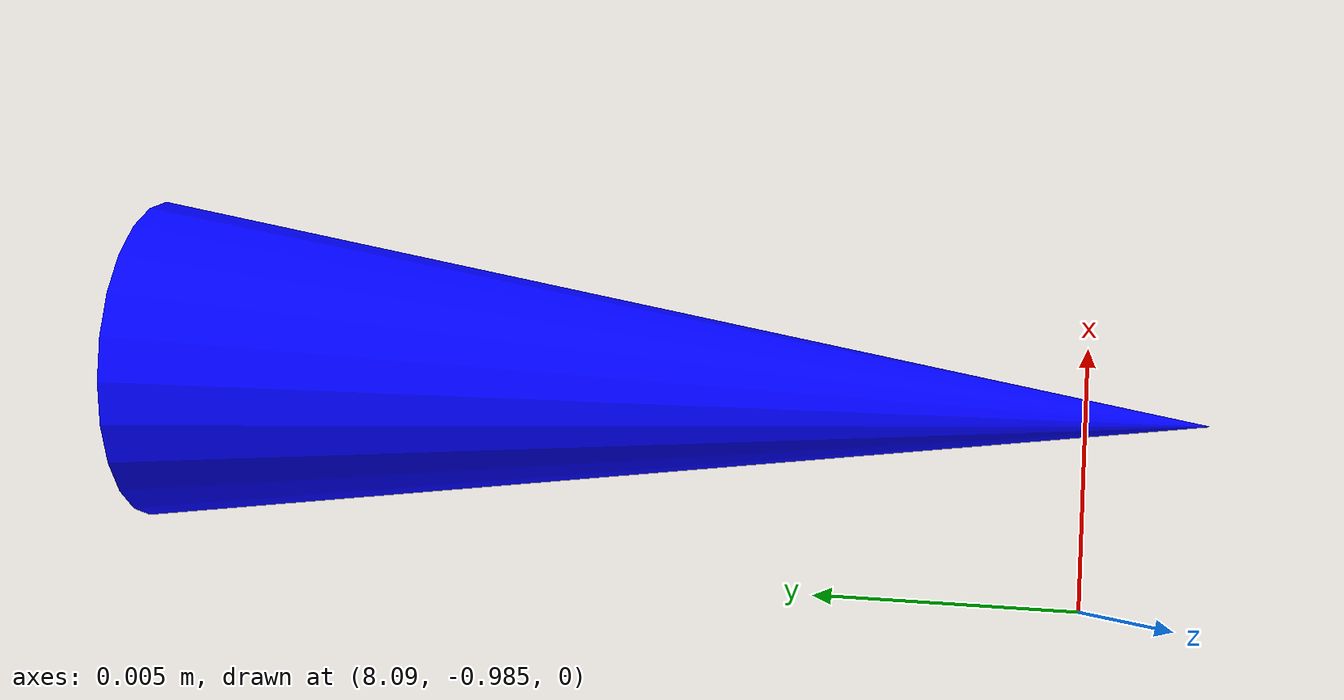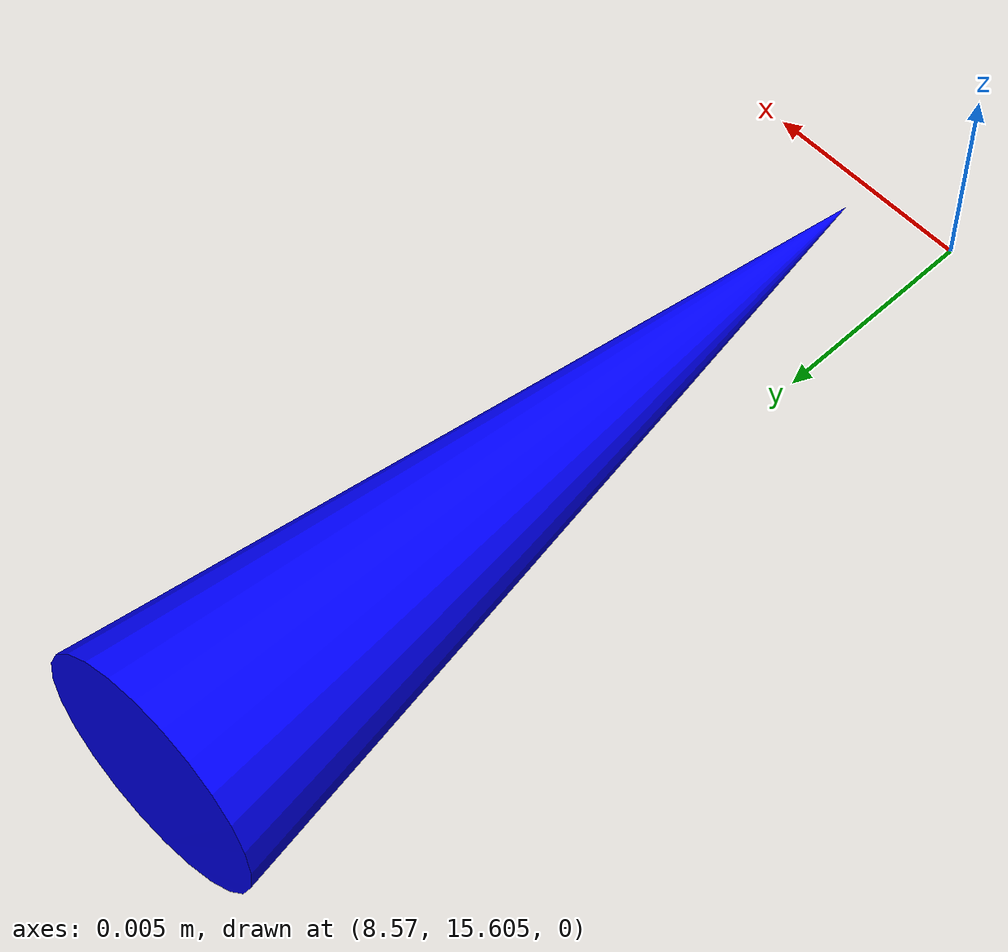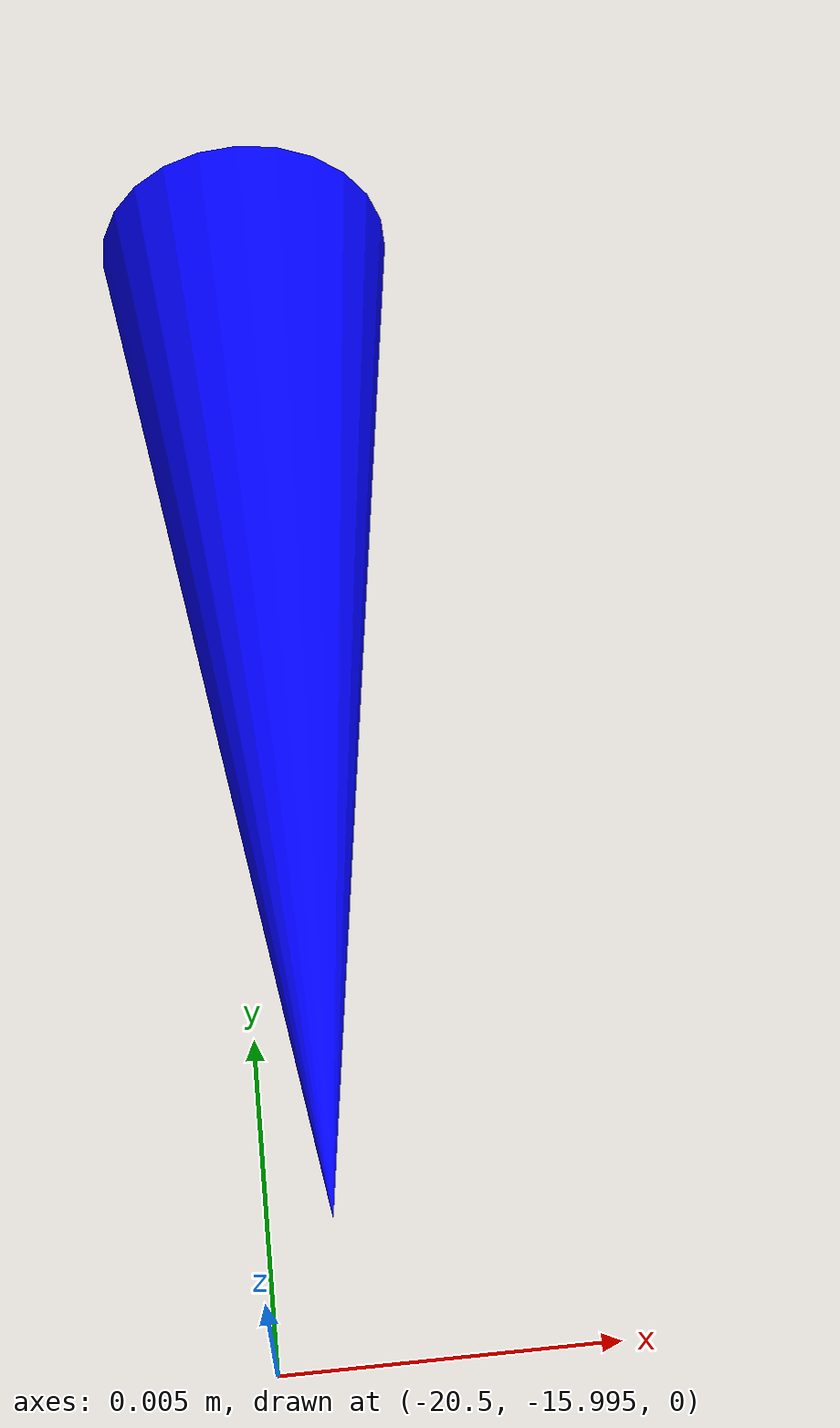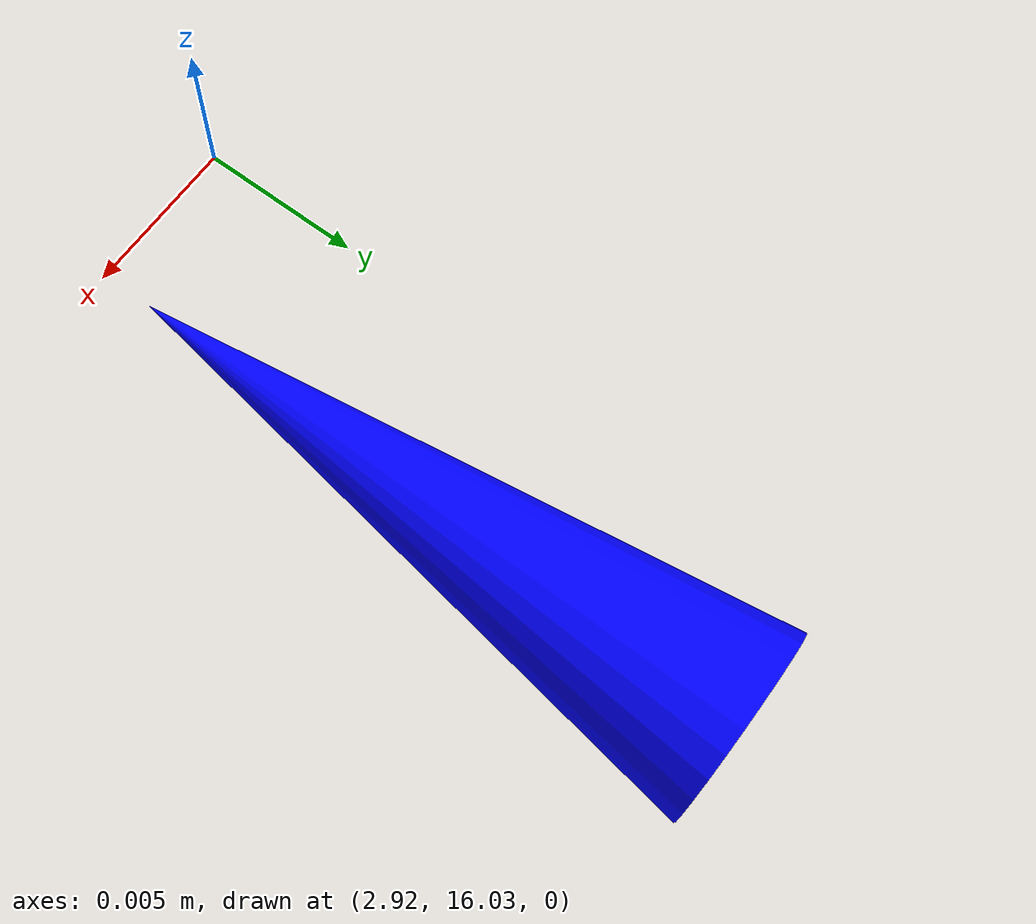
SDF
<?xml version="1.0"?>
  <sdf version='1.9'>
     <model name='cone_0'>
      <link name='cone_0_link'>
        <inertial>
			<mass>0</mass>
			<inertia>
			<ixx>0.166667</ixx>
			<ixy>0</ixy>
			<ixz>0</ixz>
			<iyy>0.166667</iyy>
			<iyz>0</iyz>
			<izz>0.166667</izz>
			</inertia>
		</inertial>
        <collision name='cone_0_collision'>
          <geometry>
            <mesh>
              <uri>/models/cone/meshes/cone.stl</uri>
              <scale>0.001 0.001 0.001</scale>
            </mesh>
          </geometry>
        </collision>
        <visual name='cone_0_visual'>
          <geometry>
            <mesh>
              <uri>/models/cone/meshes/cone.stl</uri>
              <scale>0.001 0.001 0.001</scale>
            </mesh>
          </geometry>
          <material>
            <ambient>1 1 0 1</ambient>
            <diffuse>1 1 0 1</diffuse>
            <specular>1 1 0 1</specular>
          </material>
        </visual>

        <enable_wind>false</enable_wind>
      </link>
      <pose>-0.0930312060102632 13.26364339710791 0.0 1.57 0 0</pose>
      <static>true</static>
      </model>

     <model name='cone_1'>
      <link name='cone_1_link'>
        <inertial>
			<mass>0</mass>
			<inertia>
			<ixx>0.166667</ixx>
			<ixy>0</ixy>
			<ixz>0</ixz>
			<iyy>0.166667</iyy>
			<iyz>0</iyz>
			<izz>0.166667</izz>
			</inertia>
		</inertial>
        <collision name='cone_1_collision'>
          <geometry>
            <mesh>
              <uri>/models/cone/meshes/cone.stl</uri>
              <scale>0.001 0.001 0.001</scale>
            </mesh>
          </geometry>
        </collision>
        <visual name='cone_1_visual'>
          <geometry>
            <mesh>
              <uri>/models/cone/meshes/cone.stl</uri>
              <scale>0.001 0.001 0.001</scale>
            </mesh>
          </geometry>
          <material>
            <ambient>1 1 0 1</ambient>
            <diffuse>1 1 0 1</diffuse>
            <specular>1 1 0 1</specular>
          </material>
        </visual>

        <enable_wind>false</enable_wind>
      </link>
      <pose>2.622313985945303 13.027519668355772 0.0 1.57 0 0</pose>
      <static>true</static>
      </model>

     <model name='cone_2'>
      <link name='cone_2_link'>
        <inertial>
			<mass>0</mass>
			<inertia>
			<ixx>0.166667</ixx>
			<ixy>0</ixy>
			<ixz>0</ixz>
			<iyy>0.166667</iyy>
			<iyz>0</iyz>
			<izz>0.166667</izz>
			</inertia>
		</inertial>
        <collision name='cone_2_collision'>
          <geometry>
            <mesh>
              <uri>/models/cone/meshes/cone.stl</uri>
              <scale>0.001 0.001 0.001</scale>
            </mesh>
          </geometry>
        </collision>
        <visual name='cone_2_visual'>
          <geometry>
            <mesh>
              <uri>/models/cone/meshes/cone.stl</uri>
              <scale>0.001 0.001 0.001</scale>
            </mesh>
          </geometry>
          <material>
            <ambient>1 1 0 1</ambient>
            <diffuse>1 1 0 1</diffuse>
            <specular>1 1 0 1</specular>
          </material>
        </visual>

        <enable_wind>false</enable_wind>
      </link>
      <pose>5.272074232222159 12.922969127908537 0.0 1.57 0 0</pose>
      <static>true</static>
      </model>

     <model name='cone_3'>
      <link name='cone_3_link'>
        <inertial>
			<mass>0</mass>
			<inertia>
			<ixx>0.166667</ixx>
			<ixy>0</ixy>
			<ixz>0</ixz>
			<iyy>0.166667</iyy>
			<iyz>0</iyz>
			<izz>0.166667</izz>
			</inertia>
		</inertial>
        <collision name='cone_3_collision'>
          <geometry>
            <mesh>
              <uri>/models/cone/meshes/cone.stl</uri>
              <scale>0.001 0.001 0.001</scale>
            </mesh>
          </geometry>
        </collision>
        <visual name='cone_3_visual'>
          <geometry>
            <mesh>
              <uri>/models/cone/meshes/cone.stl</uri>
              <scale>0.001 0.001 0.001</scale>
            </mesh>
          </geometry>
          <material>
            <ambient>1 1 0 1</ambient>
            <diffuse>1 1 0 1</diffuse>
            <specular>1 1 0 1</specular>
          </material>
        </visual>

        <enable_wind>false</enable_wind>
      </link>
      <pose>8.063253603102286 12.66697294832785 0.0 1.57 0 0</pose>
      <static>true</static>
      </model>

     <model name='cone_4'>
      <link name='cone_4_link'>
        <inertial>
			<mass>0</mass>
			<inertia>
			<ixx>0.166667</ixx>
			<ixy>0</ixy>
			<ixz>0</ixz>
			<iyy>0.166667</iyy>
			<iyz>0</iyz>
			<izz>0.166667</izz>
			</inertia>
		</inertial>
        <collision name='cone_4_collision'>
          <geometry>
            <mesh>
              <uri>/models/cone/meshes/cone.stl</uri>
              <scale>0.001 0.001 0.001</scale>
            </mesh>
          </geometry>
        </collision>
        <visual name='cone_4_visual'>
          <geometry>
            <mesh>
              <uri>/models/cone/meshes/cone.stl</uri>
              <scale>0.001 0.001 0.001</scale>
            </mesh>
          </geometry>
          <material>
            <ambient>1 1 0 1</ambient>
            <diffuse>1 1 0 1</diffuse>
            <specular>1 1 0 1</specular>
          </material>
        </visual>

        <enable_wind>false</enable_wind>
      </link>
      <pose>11.226056299330313 12.228174520746062 0.0 1.57 0 0</pose>
      <static>true</static>
      </model>

     <model name='cone_5'>
      <link name='cone_5_link'>
        <inertial>
			<mass>0</mass>
			<inertia>
			<ixx>0.166667</ixx>
			<ixy>0</ixy>
			<ixz>0</ixz>
			<iyy>0.166667</iyy>
			<iyz>0</iyz>
			<izz>0.166667</izz>
			</inertia>
		</inertial>
        <collision name='cone_5_collision'>
          <geometry>
            <mesh>
              <uri>/models/cone/meshes/cone.stl</uri>
              <scale>0.001 0.001 0.001</scale>
            </mesh>
          </geometry>
        </collision>
        <visual name='cone_5_visual'>
          <geometry>
            <mesh>
              <uri>/models/cone/meshes/cone.stl</uri>
              <scale>0.001 0.001 0.001</scale>
            </mesh>
          </geometry>
          <material>
            <ambient>1 1 0 1</ambient>
            <diffuse>1 1 0 1</diffuse>
            <specular>1 1 0 1</specular>
          </material>
        </visual>

        <enable_wind>false</enable_wind>
      </link>
      <pose>12.865601167799552 12.080068160310576 0.0 1.57 0 0</pose>
      <static>true</static>
      </model>

     <model name='cone_6'>
      <link name='cone_6_link'>
        <inertial>
			<mass>0</mass>
			<inertia>
			<ixx>0.166667</ixx>
			<ixy>0</ixy>
			<ixz>0</ixz>
			<iyy>0.166667</iyy>
			<iyz>0</iyz>
			<izz>0.166667</izz>
			</inertia>
		</inertial>
        <collision name='cone_6_collision'>
          <geometry>
            <mesh>
              <uri>/models/cone/meshes/cone.stl</uri>
              <scale>0.001 0.001 0.001</scale>
            </mesh>
          </geometry>
        </collision>
        <visual name='cone_6_visual'>
          <geometry>
            <mesh>
              <uri>/models/cone/meshes/cone.stl</uri>
              <scale>0.001 0.001 0.001</scale>
            </mesh>
          </geometry>
          <material>
            <ambient>1 1 0 1</ambient>
            <diffuse>1 1 0 1</diffuse>
            <specular>1 1 0 1</specular>
          </material>
        </visual>

        <enable_wind>false</enable_wind>
      </link>
      <pose>14.719470033766347 11.868433142915556 0.0 1.57 0 0</pose>
      <static>true</static>
      </model>

     <model name='cone_7'>
      <link name='cone_7_link'>
        <inertial>
			<mass>0</mass>
			<inertia>
			<ixx>0.166667</ixx>
			<ixy>0</ixy>
			<ixz>0</ixz>
			<iyy>0.166667</iyy>
			<iyz>0</iyz>
			<izz>0.166667</izz>
			</inertia>
		</inertial>
        <collision name='cone_7_collision'>
          <geometry>
            <mesh>
              <uri>/models/cone/meshes/cone.stl</uri>
              <scale>0.001 0.001 0.001</scale>
            </mesh>
          </geometry>
        </collision>
        <visual name='cone_7_visual'>
          <geometry>
            <mesh>
              <uri>/models/cone/meshes/cone.stl</uri>
              <scale>0.001 0.001 0.001</scale>
            </mesh>
          </geometry>
          <material>
            <ambient>1 1 0 1</ambient>
            <diffuse>1 1 0 1</diffuse>
            <specular>1 1 0 1</specular>
          </material>
        </visual>

        <enable_wind>false</enable_wind>
      </link>
      <pose>16.94579602253588 11.275786401048492 0.0 1.57 0 0</pose>
      <static>true</static>
      </model>

     <model name='cone_8'>
      <link name='cone_8_link'>
        <inertial>
			<mass>0</mass>
			<inertia>
			<ixx>0.166667</ixx>
			<ixy>0</ixy>
			<ixz>0</ixz>
			<iyy>0.166667</iyy>
			<iyz>0</iyz>
			<izz>0.166667</izz>
			</inertia>
		</inertial>
        <collision name='cone_8_collision'>
          <geometry>
            <mesh>
              <uri>/models/cone/meshes/cone.stl</uri>
              <scale>0.001 0.001 0.001</scale>
            </mesh>
          </geometry>
        </collision>
        <visual name='cone_8_visual'>
          <geometry>
            <mesh>
              <uri>/models/cone/meshes/cone.stl</uri>
              <scale>0.001 0.001 0.001</scale>
            </mesh>
          </geometry>
          <material>
            <ambient>1 1 0 1</ambient>
            <diffuse>1 1 0 1</diffuse>
            <specular>1 1 0 1</specular>
          </material>
        </visual>

        <enable_wind>false</enable_wind>
      </link>
      <pose>18.51991482746752 11.066607381120512 0.0 1.57 0 0</pose>
      <static>true</static>
      </model>

     <model name='cone_9'>
      <link name='cone_9_link'>
        <inertial>
			<mass>0</mass>
			<inertia>
			<ixx>0.166667</ixx>
			<ixy>0</ixy>
			<ixz>0</ixz>
			<iyy>0.166667</iyy>
			<iyz>0</iyz>
			<izz>0.166667</izz>
			</inertia>
		</inertial>
        <collision name='cone_9_collision'>
          <geometry>
            <mesh>
              <uri>/models/cone/meshes/cone.stl</uri>
              <scale>0.001 0.001 0.001</scale>
            </mesh>
          </geometry>
        </collision>
        <visual name='cone_9_visual'>
          <geometry>
            <mesh>
              <uri>/models/cone/meshes/cone.stl</uri>
              <scale>0.001 0.001 0.001</scale>
            </mesh>
          </geometry>
          <material>
            <ambient>1 1 0 1</ambient>
            <diffuse>1 1 0 1</diffuse>
            <specular>1 1 0 1</specular>
          </material>
        </visual>

        <enable_wind>false</enable_wind>
      </link>
      <pose>20.21017781269701 10.779735327974151 0.0 1.57 0 0</pose>
      <static>true</static>
      </model>

     <model name='cone_10'>
      <link name='cone_10_link'>
        <inertial>
			<mass>0</mass>
			<inertia>
			<ixx>0.166667</ixx>
			<ixy>0</ixy>
			<ixz>0</ixz>
			<iyy>0.166667</iyy>
			<iyz>0</iyz>
			<izz>0.166667</izz>
			</inertia>
		</inertial>
        <collision name='cone_10_collision'>
          <geometry>
            <mesh>
              <uri>/models/cone/meshes/cone.stl</uri>
              <scale>0.001 0.001 0.001</scale>
            </mesh>
          </geometry>
        </collision>
        <visual name='cone_10_visual'>
          <geometry>
            <mesh>
              <uri>/models/cone/meshes/cone.stl</uri>
              <scale>0.001 0.001 0.001</scale>
            </mesh>
          </geometry>
          <material>
            <ambient>1 1 0 1</ambient>
            <diffuse>1 1 0 1</diffuse>
            <specular>1 1 0 1</specular>
          </material>
        </visual>

        <enable_wind>false</enable_wind>
      </link>
      <pose>22.49556790363939 10.235237218156646 0.0 1.57 0 0</pose>
      <static>true</static>
      </model>

     <model name='cone_11'>
      <link name='cone_11_link'>
        <inertial>
			<mass>0</mass>
			<inertia>
			<ixx>0.166667</ixx>
			<ixy>0</ixy>
			<ixz>0</ixz>
			<iyy>0.166667</iyy>
			<iyz>0</iyz>
			<izz>0.166667</izz>
			</inertia>
		</inertial>
        <collision name='cone_11_collision'>
          <geometry>
            <mesh>
              <uri>/models/cone/meshes/cone.stl</uri>
              <scale>0.001 0.001 0.001</scale>
            </mesh>
          </geometry>
        </collision>
        <visual name='cone_11_visual'>
          <geometry>
            <mesh>
              <uri>/models/cone/meshes/cone.stl</uri>
              <scale>0.001 0.001 0.001</scale>
            </mesh>
          </geometry>
          <material>
            <ambient>1 1 0 1</ambient>
            <diffuse>1 1 0 1</diffuse>
            <specular>1 1 0 1</specular>
          </material>
        </visual>

        <enable_wind>false</enable_wind>
      </link>
      <pose>23.896304903151112 9.499128247514555 0.0 1.57 0 0</pose>
      <static>true</static>
      </model>

     <model name='cone_12'>
      <link name='cone_12_link'>
        <inertial>
			<mass>0</mass>
			<inertia>
			<ixx>0.166667</ixx>
			<ixy>0</ixy>
			<ixz>0</ixz>
			<iyy>0.166667</iyy>
			<iyz>0</iyz>
			<izz>0.166667</izz>
			</inertia>
		</inertial>
        <collision name='cone_12_collision'>
          <geometry>
            <mesh>
              <uri>/models/cone/meshes/cone.stl</uri>
              <scale>0.001 0.001 0.001</scale>
            </mesh>
          </geometry>
        </collision>
        <visual name='cone_12_visual'>
          <geometry>
            <mesh>
              <uri>/models/cone/meshes/cone.stl</uri>
              <scale>0.001 0.001 0.001</scale>
            </mesh>
          </geometry>
          <material>
            <ambient>1 1 0 1</ambient>
            <diffuse>1 1 0 1</diffuse>
            <specular>1 1 0 1</specular>
          </material>
        </visual>

        <enable_wind>false</enable_wind>
      </link>
      <pose>24.723218355299547 8.61242804648001 0.0 1.57 0 0</pose>
      <static>true</static>
      </model>

     <model name='cone_13'>
      <link name='cone_13_link'>
        <inertial>
			<mass>0</mass>
			<inertia>
			<ixx>0.166667</ixx>
			<ixy>0</ixy>
			<ixz>0</ixz>
			<iyy>0.166667</iyy>
			<iyz>0</iyz>
			<izz>0.166667</izz>
			</inertia>
		</inertial>
        <collision name='cone_13_collision'>
          <geometry>
            <mesh>
              <uri>/models/cone/meshes/cone.stl</uri>
              <scale>0.001 0.001 0.001</scale>
            </mesh>
          </geometry>
        </collision>
        <visual name='cone_13_visual'>
          <geometry>
            <mesh>
              <uri>/models/cone/meshes/cone.stl</uri>
              <scale>0.001 0.001 0.001</scale>
            </mesh>
          </geometry>
          <material>
            <ambient>1 1 0 1</ambient>
            <diffuse>1 1 0 1</diffuse>
            <specular>1 1 0 1</specular>
          </material>
        </visual>

        <enable_wind>false</enable_wind>
      </link>
      <pose>25.486605653883533 7.233762313142608 0.0 1.57 0 0</pose>
      <static>true</static>
      </model>

     <model name='cone_14'>
      <link name='cone_14_link'>
        <inertial>
			<mass>0</mass>
			<inertia>
			<ixx>0.166667</ixx>
			<ixy>0</ixy>
			<ixz>0</ixz>
			<iyy>0.166667</iyy>
			<iyz>0</iyz>
			<izz>0.166667</izz>
			</inertia>
		</inertial>
        <collision name='cone_14_collision'>
          <geometry>
            <mesh>
              <uri>/models/cone/meshes/cone.stl</uri>
              <scale>0.001 0.001 0.001</scale>
            </mesh>
          </geometry>
        </collision>
        <visual name='cone_14_visual'>
          <geometry>
            <mesh>
              <uri>/models/cone/meshes/cone.stl</uri>
              <scale>0.001 0.001 0.001</scale>
            </mesh>
          </geometry>
          <material>
            <ambient>1 1 0 1</ambient>
            <diffuse>1 1 0 1</diffuse>
            <specular>1 1 0 1</specular>
          </material>
        </visual>

        <enable_wind>false</enable_wind>
      </link>
      <pose>26.29800206196459 6.132768489137481 0.0 1.57 0 0</pose>
      <static>true</static>
      </model>

     <model name='cone_15'>
      <link name='cone_15_link'>
        <inertial>
			<mass>0</mass>
			<inertia>
			<ixx>0.166667</ixx>
			<ixy>0</ixy>
			<ixz>0</ixz>
			<iyy>0.166667</iyy>
			<iyz>0</iyz>
			<izz>0.166667</izz>
			</inertia>
		</inertial>
        <collision name='cone_15_collision'>
          <geometry>
            <mesh>
              <uri>/models/cone/meshes/cone.stl</uri>
              <scale>0.001 0.001 0.001</scale>
            </mesh>
          </geometry>
        </collision>
        <visual name='cone_15_visual'>
          <geometry>
            <mesh>
              <uri>/models/cone/meshes/cone.stl</uri>
              <scale>0.001 0.001 0.001</scale>
            </mesh>
          </geometry>
          <material>
            <ambient>1 1 0 1</ambient>
            <diffuse>1 1 0 1</diffuse>
            <specular>1 1 0 1</specular>
          </material>
        </visual>

        <enable_wind>false</enable_wind>
      </link>
      <pose>26.853339204908924 4.9604152214678034 0.0 1.57 0 0</pose>
      <static>true</static>
      </model>

     <model name='cone_16'>
      <link name='cone_16_link'>
        <inertial>
			<mass>0</mass>
			<inertia>
			<ixx>0.166667</ixx>
			<ixy>0</ixy>
			<ixz>0</ixz>
			<iyy>0.166667</iyy>
			<iyz>0</iyz>
			<izz>0.166667</izz>
			</inertia>
		</inertial>
        <collision name='cone_16_collision'>
          <geometry>
            <mesh>
              <uri>/models/cone/meshes/cone.stl</uri>
              <scale>0.001 0.001 0.001</scale>
            </mesh>
          </geometry>
        </collision>
        <visual name='cone_16_visual'>
          <geometry>
            <mesh>
              <uri>/models/cone/meshes/cone.stl</uri>
              <scale>0.001 0.001 0.001</scale>
            </mesh>
          </geometry>
          <material>
            <ambient>1 1 0 1</ambient>
            <diffuse>1 1 0 1</diffuse>
            <specular>1 1 0 1</specular>
          </material>
        </visual>

        <enable_wind>false</enable_wind>
      </link>
      <pose>27.029519472242907 3.743394709840606 0.0 1.57 0 0</pose>
      <static>true</static>
      </model>

     <model name='cone_17'>
      <link name='cone_17_link'>
        <inertial>
			<mass>0</mass>
			<inertia>
			<ixx>0.166667</ixx>
			<ixy>0</ixy>
			<ixz>0</ixz>
			<iyy>0.166667</iyy>
			<iyz>0</iyz>
			<izz>0.166667</izz>
			</inertia>
		</inertial>
        <collision name='cone_17_collision'>
          <geometry>
            <mesh>
              <uri>/models/cone/meshes/cone.stl</uri>
              <scale>0.001 0.001 0.001</scale>
            </mesh>
          </geometry>
        </collision>
        <visual name='cone_17_visual'>
          <geometry>
            <mesh>
              <uri>/models/cone/meshes/cone.stl</uri>
              <scale>0.001 0.001 0.001</scale>
            </mesh>
          </geometry>
          <material>
            <ambient>1 1 0 1</ambient>
            <diffuse>1 1 0 1</diffuse>
            <specular>1 1 0 1</specular>
          </material>
        </visual>

        <enable_wind>false</enable_wind>
      </link>
      <pose>26.610145387770253 2.3539770615251765 0.0 1.57 0 0</pose>
      <static>true</static>
      </model>

     <model name='cone_18'>
      <link name='cone_18_link'>
        <inertial>
			<mass>0</mass>
			<inertia>
			<ixx>0.166667</ixx>
			<ixy>0</ixy>
			<ixz>0</ixz>
			<iyy>0.166667</iyy>
			<iyz>0</iyz>
			<izz>0.166667</izz>
			</inertia>
		</inertial>
        <collision name='cone_18_collision'>
          <geometry>
            <mesh>
              <uri>/models/cone/meshes/cone.stl</uri>
              <scale>0.001 0.001 0.001</scale>
            </mesh>
          </geometry>
        </collision>
        <visual name='cone_18_visual'>
          <geometry>
            <mesh>
              <uri>/models/cone/meshes/cone.stl</uri>
              <scale>0.001 0.001 0.001</scale>
            </mesh>
          </geometry>
          <material>
            <ambient>1 1 0 1</ambient>
            <diffuse>1 1 0 1</diffuse>
            <specular>1 1 0 1</specular>
          </material>
        </visual>

        <enable_wind>false</enable_wind>
      </link>
      <pose>25.896291933180407 0.5488462937029112 0.0 1.57 0 0</pose>
      <static>true</static>
      </model>

     <model name='cone_19'>
      <link name='cone_19_link'>
        <inertial>
			<mass>0</mass>
			<inertia>
			<ixx>0.166667</ixx>
			<ixy>0</ixy>
			<ixz>0</ixz>
			<iyy>0.166667</iyy>
			<iyz>0</iyz>
			<izz>0.166667</izz>
			</inertia>
		</inertial>
        <collision name='cone_19_collision'>
          <geometry>
            <mesh>
              <uri>/models/cone/meshes/cone.stl</uri>
              <scale>0.001 0.001 0.001</scale>
            </mesh>
          </geometry>
        </collision>
        <visual name='cone_19_visual'>
          <geometry>
            <mesh>
              <uri>/models/cone/meshes/cone.stl</uri>
              <scale>0.001 0.001 0.001</scale>
            </mesh>
          </geometry>
          <material>
            <ambient>1 1 0 1</ambient>
            <diffuse>1 1 0 1</diffuse>
            <specular>1 1 0 1</specular>
          </material>
        </visual>

        <enable_wind>false</enable_wind>
      </link>
      <pose>25.14628811848314 -0.8254842269269715 0.0 1.57 0 0</pose>
      <static>true</static>
      </model>

     <model name='cone_20'>
      <link name='cone_20_link'>
        <inertial>
			<mass>0</mass>
			<inertia>
			<ixx>0.166667</ixx>
			<ixy>0</ixy>
			<ixz>0</ixz>
			<iyy>0.166667</iyy>
			<iyz>0</iyz>
			<izz>0.166667</izz>
			</inertia>
		</inertial>
        <collision name='cone_20_collision'>
          <geometry>
            <mesh>
              <uri>/models/cone/meshes/cone.stl</uri>
              <scale>0.001 0.001 0.001</scale>
            </mesh>
          </geometry>
        </collision>
        <visual name='cone_20_visual'>
          <geometry>
            <mesh>
              <uri>/models/cone/meshes/cone.stl</uri>
              <scale>0.001 0.001 0.001</scale>
            </mesh>
          </geometry>
          <material>
            <ambient>1 1 0 1</ambient>
            <diffuse>1 1 0 1</diffuse>
            <specular>1 1 0 1</specular>
          </material>
        </visual>

        <enable_wind>false</enable_wind>
      </link>
      <pose>24.223698244215562 -1.7898320662824403 0.0 1.57 0 0</pose>
      <static>true</static>
      </model>

     <model name='cone_21'>
      <link name='cone_21_link'>
        <inertial>
			<mass>0</mass>
			<inertia>
			<ixx>0.166667</ixx>
			<ixy>0</ixy>
			<ixz>0</ixz>
			<iyy>0.166667</iyy>
			<iyz>0</iyz>
			<izz>0.166667</izz>
			</inertia>
		</inertial>
        <collision name='cone_21_collision'>
          <geometry>
            <mesh>
              <uri>/models/cone/meshes/cone.stl</uri>
              <scale>0.001 0.001 0.001</scale>
            </mesh>
          </geometry>
        </collision>
        <visual name='cone_21_visual'>
          <geometry>
            <mesh>
              <uri>/models/cone/meshes/cone.stl</uri>
              <scale>0.001 0.001 0.001</scale>
            </mesh>
          </geometry>
          <material>
            <ambient>1 1 0 1</ambient>
            <diffuse>1 1 0 1</diffuse>
            <specular>1 1 0 1</specular>
          </material>
        </visual>

        <enable_wind>false</enable_wind>
      </link>
      <pose>22.96590977680834 -2.717463444456268 0.0 1.57 0 0</pose>
      <static>true</static>
      </model>

     <model name='cone_22'>
      <link name='cone_22_link'>
        <inertial>
			<mass>0</mass>
			<inertia>
			<ixx>0.166667</ixx>
			<ixy>0</ixy>
			<ixz>0</ixz>
			<iyy>0.166667</iyy>
			<iyz>0</iyz>
			<izz>0.166667</izz>
			</inertia>
		</inertial>
        <collision name='cone_22_collision'>
          <geometry>
            <mesh>
              <uri>/models/cone/meshes/cone.stl</uri>
              <scale>0.001 0.001 0.001</scale>
            </mesh>
          </geometry>
        </collision>
        <visual name='cone_22_visual'>
          <geometry>
            <mesh>
              <uri>/models/cone/meshes/cone.stl</uri>
              <scale>0.001 0.001 0.001</scale>
            </mesh>
          </geometry>
          <material>
            <ambient>1 1 0 1</ambient>
            <diffuse>1 1 0 1</diffuse>
            <specular>1 1 0 1</specular>
          </material>
        </visual>

        <enable_wind>false</enable_wind>
      </link>
      <pose>21.908157930494863 -3.289301632627655 0.0 1.57 0 0</pose>
      <static>true</static>
      </model>

     <model name='cone_23'>
      <link name='cone_23_link'>
        <inertial>
			<mass>0</mass>
			<inertia>
			<ixx>0.166667</ixx>
			<ixy>0</ixy>
			<ixz>0</ixz>
			<iyy>0.166667</iyy>
			<iyz>0</iyz>
			<izz>0.166667</izz>
			</inertia>
		</inertial>
        <collision name='cone_23_collision'>
          <geometry>
            <mesh>
              <uri>/models/cone/meshes/cone.stl</uri>
              <scale>0.001 0.001 0.001</scale>
            </mesh>
          </geometry>
        </collision>
        <visual name='cone_23_visual'>
          <geometry>
            <mesh>
              <uri>/models/cone/meshes/cone.stl</uri>
              <scale>0.001 0.001 0.001</scale>
            </mesh>
          </geometry>
          <material>
            <ambient>1 1 0 1</ambient>
            <diffuse>1 1 0 1</diffuse>
            <specular>1 1 0 1</specular>
          </material>
        </visual>

        <enable_wind>false</enable_wind>
      </link>
      <pose>20.74481488239916 -3.6980252730695495 0.0 1.57 0 0</pose>
      <static>true</static>
      </model>

     <model name='cone_24'>
      <link name='cone_24_link'>
        <inertial>
			<mass>0</mass>
			<inertia>
			<ixx>0.166667</ixx>
			<ixy>0</ixy>
			<ixz>0</ixz>
			<iyy>0.166667</iyy>
			<iyz>0</iyz>
			<izz>0.166667</izz>
			</inertia>
		</inertial>
        <collision name='cone_24_collision'>
          <geometry>
            <mesh>
              <uri>/models/cone/meshes/cone.stl</uri>
              <scale>0.001 0.001 0.001</scale>
            </mesh>
          </geometry>
        </collision>
        <visual name='cone_24_visual'>
          <geometry>
            <mesh>
              <uri>/models/cone/meshes/cone.stl</uri>
              <scale>0.001 0.001 0.001</scale>
            </mesh>
          </geometry>
          <material>
            <ambient>1 1 0 1</ambient>
            <diffuse>1 1 0 1</diffuse>
            <specular>1 1 0 1</specular>
          </material>
        </visual>

        <enable_wind>false</enable_wind>
      </link>
      <pose>18.914652834059318 -4.286176251157928 0.0 1.57 0 0</pose>
      <static>true</static>
      </model>

     <model name='cone_25'>
      <link name='cone_25_link'>
        <inertial>
			<mass>0</mass>
			<inertia>
			<ixx>0.166667</ixx>
			<ixy>0</ixy>
			<ixz>0</ixz>
			<iyy>0.166667</iyy>
			<iyz>0</iyz>
			<izz>0.166667</izz>
			</inertia>
		</inertial>
        <collision name='cone_25_collision'>
          <geometry>
            <mesh>
              <uri>/models/cone/meshes/cone.stl</uri>
              <scale>0.001 0.001 0.001</scale>
            </mesh>
          </geometry>
        </collision>
        <visual name='cone_25_visual'>
          <geometry>
            <mesh>
              <uri>/models/cone/meshes/cone.stl</uri>
              <scale>0.001 0.001 0.001</scale>
            </mesh>
          </geometry>
          <material>
            <ambient>1 1 0 1</ambient>
            <diffuse>1 1 0 1</diffuse>
            <specular>1 1 0 1</specular>
          </material>
        </visual>

        <enable_wind>false</enable_wind>
      </link>
      <pose>17.064981660963614 -4.491789768919158 0.0 1.57 0 0</pose>
      <static>true</static>
      </model>

     <model name='cone_26'>
      <link name='cone_26_link'>
        <inertial>
			<mass>0</mass>
			<inertia>
			<ixx>0.166667</ixx>
			<ixy>0</ixy>
			<ixz>0</ixz>
			<iyy>0.166667</iyy>
			<iyz>0</iyz>
			<izz>0.166667</izz>
			</inertia>
		</inertial>
        <collision name='cone_26_collision'>
          <geometry>
            <mesh>
              <uri>/models/cone/meshes/cone.stl</uri>
              <scale>0.001 0.001 0.001</scale>
            </mesh>
          </geometry>
        </collision>
        <visual name='cone_26_visual'>
          <geometry>
            <mesh>
              <uri>/models/cone/meshes/cone.stl</uri>
              <scale>0.001 0.001 0.001</scale>
            </mesh>
          </geometry>
          <material>
            <ambient>1 1 0 1</ambient>
            <diffuse>1 1 0 1</diffuse>
            <specular>1 1 0 1</specular>
          </material>
        </visual>

        <enable_wind>false</enable_wind>
      </link>
      <pose>15.5014625645891 -4.486052654966522 0.0 1.57 0 0</pose>
      <static>true</static>
      </model>

     <model name='cone_27'>
      <link name='cone_27_link'>
        <inertial>
			<mass>0</mass>
			<inertia>
			<ixx>0.166667</ixx>
			<ixy>0</ixy>
			<ixz>0</ixz>
			<iyy>0.166667</iyy>
			<iyz>0</iyz>
			<izz>0.166667</izz>
			</inertia>
		</inertial>
        <collision name='cone_27_collision'>
          <geometry>
            <mesh>
              <uri>/models/cone/meshes/cone.stl</uri>
              <scale>0.001 0.001 0.001</scale>
            </mesh>
          </geometry>
        </collision>
        <visual name='cone_27_visual'>
          <geometry>
            <mesh>
              <uri>/models/cone/meshes/cone.stl</uri>
              <scale>0.001 0.001 0.001</scale>
            </mesh>
          </geometry>
          <material>
            <ambient>1 1 0 1</ambient>
            <diffuse>1 1 0 1</diffuse>
            <specular>1 1 0 1</specular>
          </material>
        </visual>

        <enable_wind>false</enable_wind>
      </link>
      <pose>13.84660759937914 -4.0115117537824405 0.0 1.57 0 0</pose>
      <static>true</static>
      </model>

     <model name='cone_28'>
      <link name='cone_28_link'>
        <inertial>
			<mass>0</mass>
			<inertia>
			<ixx>0.166667</ixx>
			<ixy>0</ixy>
			<ixz>0</ixz>
			<iyy>0.166667</iyy>
			<iyz>0</iyz>
			<izz>0.166667</izz>
			</inertia>
		</inertial>
        <collision name='cone_28_collision'>
          <geometry>
            <mesh>
              <uri>/models/cone/meshes/cone.stl</uri>
              <scale>0.001 0.001 0.001</scale>
            </mesh>
          </geometry>
        </collision>
        <visual name='cone_28_visual'>
          <geometry>
            <mesh>
              <uri>/models/cone/meshes/cone.stl</uri>
              <scale>0.001 0.001 0.001</scale>
            </mesh>
          </geometry>
          <material>
            <ambient>1 1 0 1</ambient>
            <diffuse>1 1 0 1</diffuse>
            <specular>1 1 0 1</specular>
          </material>
        </visual>

        <enable_wind>false</enable_wind>
      </link>
      <pose>12.792988023878653 -3.4147317397443544 0.0 1.57 0 0</pose>
      <static>true</static>
      </model>

     <model name='cone_29'>
      <link name='cone_29_link'>
        <inertial>
			<mass>0</mass>
			<inertia>
			<ixx>0.166667</ixx>
			<ixy>0</ixy>
			<ixz>0</ixz>
			<iyy>0.166667</iyy>
			<iyz>0</iyz>
			<izz>0.166667</izz>
			</inertia>
		</inertial>
        <collision name='cone_29_collision'>
          <geometry>
            <mesh>
              <uri>/models/cone/meshes/cone.stl</uri>
              <scale>0.001 0.001 0.001</scale>
            </mesh>
          </geometry>
        </collision>
        <visual name='cone_29_visual'>
          <geometry>
            <mesh>
              <uri>/models/cone/meshes/cone.stl</uri>
              <scale>0.001 0.001 0.001</scale>
            </mesh>
          </geometry>
          <material>
            <ambient>1 1 0 1</ambient>
            <diffuse>1 1 0 1</diffuse>
            <specular>1 1 0 1</specular>
          </material>
        </visual>

        <enable_wind>false</enable_wind>
      </link>
      <pose>11.91996537220629 -2.6046103942243346 0.0 1.57 0 0</pose>
      <static>true</static>
      </model>

     <model name='cone_30'>
      <link name='cone_30_link'>
        <inertial>
			<mass>0</mass>
			<inertia>
			<ixx>0.166667</ixx>
			<ixy>0</ixy>
			<ixz>0</ixz>
			<iyy>0.166667</iyy>
			<iyz>0</iyz>
			<izz>0.166667</izz>
			</inertia>
		</inertial>
        <collision name='cone_30_collision'>
          <geometry>
            <mesh>
              <uri>/models/cone/meshes/cone.stl</uri>
              <scale>0.001 0.001 0.001</scale>
            </mesh>
          </geometry>
        </collision>
        <visual name='cone_30_visual'>
          <geometry>
            <mesh>
              <uri>/models/cone/meshes/cone.stl</uri>
              <scale>0.001 0.001 0.001</scale>
            </mesh>
          </geometry>
          <material>
            <ambient>1 1 0 1</ambient>
            <diffuse>1 1 0 1</diffuse>
            <specular>1 1 0 1</specular>
          </material>
        </visual>

        <enable_wind>false</enable_wind>
      </link>
      <pose>10.578062830092032 -1.2908994185773621 0.0 1.57 0 0</pose>
      <static>true</static>
      </model>

     <model name='cone_31'>
      <link name='cone_31_link'>
        <inertial>
			<mass>0</mass>
			<inertia>
			<ixx>0.166667</ixx>
			<ixy>0</ixy>
			<ixz>0</ixz>
			<iyy>0.166667</iyy>
			<iyz>0</iyz>
			<izz>0.166667</izz>
			</inertia>
		</inertial>
        <collision name='cone_31_collision'>
          <geometry>
            <mesh>
              <uri>/models/cone/meshes/cone.stl</uri>
              <scale>0.001 0.001 0.001</scale>
            </mesh>
          </geometry>
        </collision>
        <visual name='cone_31_visual'>
          <geometry>
            <mesh>
              <uri>/models/cone/meshes/cone.stl</uri>
              <scale>0.001 0.001 0.001</scale>
            </mesh>
          </geometry>
          <material>
            <ambient>1 1 0 1</ambient>
            <diffuse>1 1 0 1</diffuse>
            <specular>1 1 0 1</specular>
          </material>
        </visual>

        <enable_wind>false</enable_wind>
      </link>
      <pose>9.2347784138933 0.13272862555105575 0.0 1.57 0 0</pose>
      <static>true</static>
      </model>

     <model name='cone_32'>
      <link name='cone_32_link'>
        <inertial>
			<mass>0</mass>
			<inertia>
			<ixx>0.166667</ixx>
			<ixy>0</ixy>
			<ixz>0</ixz>
			<iyy>0.166667</iyy>
			<iyz>0</iyz>
			<izz>0.166667</izz>
			</inertia>
		</inertial>
        <collision name='cone_32_collision'>
          <geometry>
            <mesh>
              <uri>/models/cone/meshes/cone.stl</uri>
              <scale>0.001 0.001 0.001</scale>
            </mesh>
          </geometry>
        </collision>
        <visual name='cone_32_visual'>
          <geometry>
            <mesh>
              <uri>/models/cone/meshes/cone.stl</uri>
              <scale>0.001 0.001 0.001</scale>
            </mesh>
          </geometry>
          <material>
            <ambient>1 1 0 1</ambient>
            <diffuse>1 1 0 1</diffuse>
            <specular>1 1 0 1</specular>
          </material>
        </visual>

        <enable_wind>false</enable_wind>
      </link>
      <pose>7.737128648878653 1.2848190796526182 0.0 1.57 0 0</pose>
      <static>true</static>
      </model>

     <model name='cone_33'>
      <link name='cone_33_link'>
        <inertial>
			<mass>0</mass>
			<inertia>
			<ixx>0.166667</ixx>
			<ixy>0</ixy>
			<ixz>0</ixz>
			<iyy>0.166667</iyy>
			<iyz>0</iyz>
			<izz>0.166667</izz>
			</inertia>
		</inertial>
        <collision name='cone_33_collision'>
          <geometry>
            <mesh>
              <uri>/models/cone/meshes/cone.stl</uri>
              <scale>0.001 0.001 0.001</scale>
            </mesh>
          </geometry>
        </collision>
        <visual name='cone_33_visual'>
          <geometry>
            <mesh>
              <uri>/models/cone/meshes/cone.stl</uri>
              <scale>0.001 0.001 0.001</scale>
            </mesh>
          </geometry>
          <material>
            <ambient>1 1 0 1</ambient>
            <diffuse>1 1 0 1</diffuse>
            <specular>1 1 0 1</specular>
          </material>
        </visual>

        <enable_wind>false</enable_wind>
      </link>
      <pose>5.821543417097647 2.133885241761993 0.0 1.57 0 0</pose>
      <static>true</static>
      </model>

     <model name='cone_34'>
      <link name='cone_34_link'>
        <inertial>
			<mass>0</mass>
			<inertia>
			<ixx>0.166667</ixx>
			<ixy>0</ixy>
			<ixz>0</ixz>
			<iyy>0.166667</iyy>
			<iyz>0</iyz>
			<izz>0.166667</izz>
			</inertia>
		</inertial>
        <collision name='cone_34_collision'>
          <geometry>
            <mesh>
              <uri>/models/cone/meshes/cone.stl</uri>
              <scale>0.001 0.001 0.001</scale>
            </mesh>
          </geometry>
        </collision>
        <visual name='cone_34_visual'>
          <geometry>
            <mesh>
              <uri>/models/cone/meshes/cone.stl</uri>
              <scale>0.001 0.001 0.001</scale>
            </mesh>
          </geometry>
          <material>
            <ambient>1 1 0 1</ambient>
            <diffuse>1 1 0 1</diffuse>
            <specular>1 1 0 1</specular>
          </material>
        </visual>

        <enable_wind>false</enable_wind>
      </link>
      <pose>3.914461717726309 2.804799128785919 0.0 1.57 0 0</pose>
      <static>true</static>
      </model>

     <model name='cone_35'>
      <link name='cone_35_link'>
        <inertial>
			<mass>0</mass>
			<inertia>
			<ixx>0.166667</ixx>
			<ixy>0</ixy>
			<ixz>0</ixz>
			<iyy>0.166667</iyy>
			<iyz>0</iyz>
			<izz>0.166667</izz>
			</inertia>
		</inertial>
        <collision name='cone_35_collision'>
          <geometry>
            <mesh>
              <uri>/models/cone/meshes/cone.stl</uri>
              <scale>0.001 0.001 0.001</scale>
            </mesh>
          </geometry>
        </collision>
        <visual name='cone_35_visual'>
          <geometry>
            <mesh>
              <uri>/models/cone/meshes/cone.stl</uri>
              <scale>0.001 0.001 0.001</scale>
            </mesh>
          </geometry>
          <material>
            <ambient>1 1 0 1</ambient>
            <diffuse>1 1 0 1</diffuse>
            <specular>1 1 0 1</specular>
          </material>
        </visual>

        <enable_wind>false</enable_wind>
      </link>
      <pose>1.8161630250230618 3.1757154953630673 0.0 1.57 0 0</pose>
      <static>true</static>
      </model>

     <model name='cone_36'>
      <link name='cone_36_link'>
        <inertial>
			<mass>0</mass>
			<inertia>
			<ixx>0.166667</ixx>
			<ixy>0</ixy>
			<ixz>0</ixz>
			<iyy>0.166667</iyy>
			<iyz>0</iyz>
			<izz>0.166667</izz>
			</inertia>
		</inertial>
        <collision name='cone_36_collision'>
          <geometry>
            <mesh>
              <uri>/models/cone/meshes/cone.stl</uri>
              <scale>0.001 0.001 0.001</scale>
            </mesh>
          </geometry>
        </collision>
        <visual name='cone_36_visual'>
          <geometry>
            <mesh>
              <uri>/models/cone/meshes/cone.stl</uri>
              <scale>0.001 0.001 0.001</scale>
            </mesh>
          </geometry>
          <material>
            <ambient>1 1 0 1</ambient>
            <diffuse>1 1 0 1</diffuse>
            <specular>1 1 0 1</specular>
          </material>
        </visual>

        <enable_wind>false</enable_wind>
      </link>
      <pose>-0.3473444365247895 3.618542052522491 0.0 1.57 0 0</pose>
      <static>true</static>
      </model>

     <model name='cone_37'>
      <link name='cone_37_link'>
        <inertial>
			<mass>0</mass>
			<inertia>
			<ixx>0.166667</ixx>
			<ixy>0</ixy>
			<ixz>0</ixz>
			<iyy>0.166667</iyy>
			<iyz>0</iyz>
			<izz>0.166667</izz>
			</inertia>
		</inertial>
        <collision name='cone_37_collision'>
          <geometry>
            <mesh>
              <uri>/models/cone/meshes/cone.stl</uri>
              <scale>0.001 0.001 0.001</scale>
            </mesh>
          </geometry>
        </collision>
        <visual name='cone_37_visual'>
          <geometry>
            <mesh>
              <uri>/models/cone/meshes/cone.stl</uri>
              <scale>0.001 0.001 0.001</scale>
            </mesh>
          </geometry>
          <material>
            <ambient>1 1 0 1</ambient>
            <diffuse>1 1 0 1</diffuse>
            <specular>1 1 0 1</specular>
          </material>
        </visual>

        <enable_wind>false</enable_wind>
      </link>
      <pose>-2.3448894880994966 3.4681380760820613 0.0 1.57 0 0</pose>
      <static>true</static>
      </model>

     <model name='cone_38'>
      <link name='cone_38_link'>
        <inertial>
			<mass>0</mass>
			<inertia>
			<ixx>0.166667</ixx>
			<ixy>0</ixy>
			<ixz>0</ixz>
			<iyy>0.166667</iyy>
			<iyz>0</iyz>
			<izz>0.166667</izz>
			</inertia>
		</inertial>
        <collision name='cone_38_collision'>
          <geometry>
            <mesh>
              <uri>/models/cone/meshes/cone.stl</uri>
              <scale>0.001 0.001 0.001</scale>
            </mesh>
          </geometry>
        </collision>
        <visual name='cone_38_visual'>
          <geometry>
            <mesh>
              <uri>/models/cone/meshes/cone.stl</uri>
              <scale>0.001 0.001 0.001</scale>
            </mesh>
          </geometry>
          <material>
            <ambient>1 1 0 1</ambient>
            <diffuse>1 1 0 1</diffuse>
            <specular>1 1 0 1</specular>
          </material>
        </visual>

        <enable_wind>false</enable_wind>
      </link>
      <pose>-4.2419776343092135 2.8697058212908018 0.0 1.57 0 0</pose>
      <static>true</static>
      </model>

     <model name='cone_39'>
      <link name='cone_39_link'>
        <inertial>
			<mass>0</mass>
			<inertia>
			<ixx>0.166667</ixx>
			<ixy>0</ixy>
			<ixz>0</ixz>
			<iyy>0.166667</iyy>
			<iyz>0</iyz>
			<izz>0.166667</izz>
			</inertia>
		</inertial>
        <collision name='cone_39_collision'>
          <geometry>
            <mesh>
              <uri>/models/cone/meshes/cone.stl</uri>
              <scale>0.001 0.001 0.001</scale>
            </mesh>
          </geometry>
        </collision>
        <visual name='cone_39_visual'>
          <geometry>
            <mesh>
              <uri>/models/cone/meshes/cone.stl</uri>
              <scale>0.001 0.001 0.001</scale>
            </mesh>
          </geometry>
          <material>
            <ambient>1 1 0 1</ambient>
            <diffuse>1 1 0 1</diffuse>
            <specular>1 1 0 1</specular>
          </material>
        </visual>

        <enable_wind>false</enable_wind>
      </link>
      <pose>-5.682290472863595 1.8797325623186338 0.0 1.57 0 0</pose>
      <static>true</static>
      </model>

     <model name='cone_40'>
      <link name='cone_40_link'>
        <inertial>
			<mass>0</mass>
			<inertia>
			<ixx>0.166667</ixx>
			<ixy>0</ixy>
			<ixz>0</ixz>
			<iyy>0.166667</iyy>
			<iyz>0</iyz>
			<izz>0.166667</izz>
			</inertia>
		</inertial>
        <collision name='cone_40_collision'>
          <geometry>
            <mesh>
              <uri>/models/cone/meshes/cone.stl</uri>
              <scale>0.001 0.001 0.001</scale>
            </mesh>
          </geometry>
        </collision>
        <visual name='cone_40_visual'>
          <geometry>
            <mesh>
              <uri>/models/cone/meshes/cone.stl</uri>
              <scale>0.001 0.001 0.001</scale>
            </mesh>
          </geometry>
          <material>
            <ambient>1 1 0 1</ambient>
            <diffuse>1 1 0 1</diffuse>
            <specular>1 1 0 1</specular>
          </material>
        </visual>

        <enable_wind>false</enable_wind>
      </link>
      <pose>-6.784324207185189 0.7649353516252745 0.0 1.57 0 0</pose>
      <static>true</static>
      </model>

     <model name='cone_41'>
      <link name='cone_41_link'>
        <inertial>
			<mass>0</mass>
			<inertia>
			<ixx>0.166667</ixx>
			<ixy>0</ixy>
			<ixz>0</ixz>
			<iyy>0.166667</iyy>
			<iyz>0</iyz>
			<izz>0.166667</izz>
			</inertia>
		</inertial>
        <collision name='cone_41_collision'>
          <geometry>
            <mesh>
              <uri>/models/cone/meshes/cone.stl</uri>
              <scale>0.001 0.001 0.001</scale>
            </mesh>
          </geometry>
        </collision>
        <visual name='cone_41_visual'>
          <geometry>
            <mesh>
              <uri>/models/cone/meshes/cone.stl</uri>
              <scale>0.001 0.001 0.001</scale>
            </mesh>
          </geometry>
          <material>
            <ambient>1 1 0 1</ambient>
            <diffuse>1 1 0 1</diffuse>
            <specular>1 1 0 1</specular>
          </material>
        </visual>

        <enable_wind>false</enable_wind>
      </link>
      <pose>-7.940333642838875 -0.6019797789899598 0.0 1.57 0 0</pose>
      <static>true</static>
      </model>

     <model name='cone_42'>
      <link name='cone_42_link'>
        <inertial>
			<mass>0</mass>
			<inertia>
			<ixx>0.166667</ixx>
			<ixy>0</ixy>
			<ixz>0</ixz>
			<iyy>0.166667</iyy>
			<iyz>0</iyz>
			<izz>0.166667</izz>
			</inertia>
		</inertial>
        <collision name='cone_42_collision'>
          <geometry>
            <mesh>
              <uri>/models/cone/meshes/cone.stl</uri>
              <scale>0.001 0.001 0.001</scale>
            </mesh>
          </geometry>
        </collision>
        <visual name='cone_42_visual'>
          <geometry>
            <mesh>
              <uri>/models/cone/meshes/cone.stl</uri>
              <scale>0.001 0.001 0.001</scale>
            </mesh>
          </geometry>
          <material>
            <ambient>1 1 0 1</ambient>
            <diffuse>1 1 0 1</diffuse>
            <specular>1 1 0 1</specular>
          </material>
        </visual>

        <enable_wind>false</enable_wind>
      </link>
      <pose>-8.848003949998299 -3.433395718321014 0.0 1.57 0 0</pose>
      <static>true</static>
      </model>

     <model name='cone_43'>
      <link name='cone_43_link'>
        <inertial>
			<mass>0</mass>
			<inertia>
			<ixx>0.166667</ixx>
			<ixy>0</ixy>
			<ixz>0</ixz>
			<iyy>0.166667</iyy>
			<iyz>0</iyz>
			<izz>0.166667</izz>
			</inertia>
		</inertial>
        <collision name='cone_43_collision'>
          <geometry>
            <mesh>
              <uri>/models/cone/meshes/cone.stl</uri>
              <scale>0.001 0.001 0.001</scale>
            </mesh>
          </geometry>
        </collision>
        <visual name='cone_43_visual'>
          <geometry>
            <mesh>
              <uri>/models/cone/meshes/cone.stl</uri>
              <scale>0.001 0.001 0.001</scale>
            </mesh>
          </geometry>
          <material>
            <ambient>1 1 0 1</ambient>
            <diffuse>1 1 0 1</diffuse>
            <specular>1 1 0 1</specular>
          </material>
        </visual>

        <enable_wind>false</enable_wind>
      </link>
      <pose>-9.66509675013868 -5.638050984129119 0.0 1.57 0 0</pose>
      <static>true</static>
      </model>

     <model name='cone_44'>
      <link name='cone_44_link'>
        <inertial>
			<mass>0</mass>
			<inertia>
			<ixx>0.166667</ixx>
			<ixy>0</ixy>
			<ixz>0</ixz>
			<iyy>0.166667</iyy>
			<iyz>0</iyz>
			<izz>0.166667</izz>
			</inertia>
		</inertial>
        <collision name='cone_44_collision'>
          <geometry>
            <mesh>
              <uri>/models/cone/meshes/cone.stl</uri>
              <scale>0.001 0.001 0.001</scale>
            </mesh>
          </geometry>
        </collision>
        <visual name='cone_44_visual'>
          <geometry>
            <mesh>
              <uri>/models/cone/meshes/cone.stl</uri>
              <scale>0.001 0.001 0.001</scale>
            </mesh>
          </geometry>
          <material>
            <ambient>1 1 0 1</ambient>
            <diffuse>1 1 0 1</diffuse>
            <specular>1 1 0 1</specular>
          </material>
        </visual>

        <enable_wind>false</enable_wind>
      </link>
      <pose>-10.765136613725106 -7.091470097288299 0.0 1.57 0 0</pose>
      <static>true</static>
      </model>

     <model name='cone_45'>
      <link name='cone_45_link'>
        <inertial>
			<mass>0</mass>
			<inertia>
			<ixx>0.166667</ixx>
			<ixy>0</ixy>
			<ixz>0</ixz>
			<iyy>0.166667</iyy>
			<iyz>0</iyz>
			<izz>0.166667</izz>
			</inertia>
		</inertial>
        <collision name='cone_45_collision'>
          <geometry>
            <mesh>
              <uri>/models/cone/meshes/cone.stl</uri>
              <scale>0.001 0.001 0.001</scale>
            </mesh>
          </geometry>
        </collision>
        <visual name='cone_45_visual'>
          <geometry>
            <mesh>
              <uri>/models/cone/meshes/cone.stl</uri>
              <scale>0.001 0.001 0.001</scale>
            </mesh>
          </geometry>
          <material>
            <ambient>1 1 0 1</ambient>
            <diffuse>1 1 0 1</diffuse>
            <specular>1 1 0 1</specular>
          </material>
        </visual>

        <enable_wind>false</enable_wind>
      </link>
      <pose>-11.945099534867683 -9.488009594663787 0.0 1.57 0 0</pose>
      <static>true</static>
      </model>

     <model name='cone_46'>
      <link name='cone_46_link'>
        <inertial>
			<mass>0</mass>
			<inertia>
			<ixx>0.166667</ixx>
			<ixy>0</ixy>
			<ixz>0</ixz>
			<iyy>0.166667</iyy>
			<iyz>0</iyz>
			<izz>0.166667</izz>
			</inertia>
		</inertial>
        <collision name='cone_46_collision'>
          <geometry>
            <mesh>
              <uri>/models/cone/meshes/cone.stl</uri>
              <scale>0.001 0.001 0.001</scale>
            </mesh>
          </geometry>
        </collision>
        <visual name='cone_46_visual'>
          <geometry>
            <mesh>
              <uri>/models/cone/meshes/cone.stl</uri>
              <scale>0.001 0.001 0.001</scale>
            </mesh>
          </geometry>
          <material>
            <ambient>1 1 0 1</ambient>
            <diffuse>1 1 0 1</diffuse>
            <specular>1 1 0 1</specular>
          </material>
        </visual>

        <enable_wind>false</enable_wind>
      </link>
      <pose>-12.095192422746102 -11.285356472715545 0.0 1.57 0 0</pose>
      <static>true</static>
      </model>

     <model name='cone_47'>
      <link name='cone_47_link'>
        <inertial>
			<mass>0</mass>
			<inertia>
			<ixx>0.166667</ixx>
			<ixy>0</ixy>
			<ixz>0</ixz>
			<iyy>0.166667</iyy>
			<iyz>0</iyz>
			<izz>0.166667</izz>
			</inertia>
		</inertial>
        <collision name='cone_47_collision'>
          <geometry>
            <mesh>
              <uri>/models/cone/meshes/cone.stl</uri>
              <scale>0.001 0.001 0.001</scale>
            </mesh>
          </geometry>
        </collision>
        <visual name='cone_47_visual'>
          <geometry>
            <mesh>
              <uri>/models/cone/meshes/cone.stl</uri>
              <scale>0.001 0.001 0.001</scale>
            </mesh>
          </geometry>
          <material>
            <ambient>1 1 0 1</ambient>
            <diffuse>1 1 0 1</diffuse>
            <specular>1 1 0 1</specular>
          </material>
        </visual>

        <enable_wind>false</enable_wind>
      </link>
      <pose>-11.793469228623787 -13.106327389463592 0.0 1.57 0 0</pose>
      <static>true</static>
      </model>

     <model name='cone_48'>
      <link name='cone_48_link'>
        <inertial>
			<mass>0</mass>
			<inertia>
			<ixx>0.166667</ixx>
			<ixy>0</ixy>
			<ixz>0</ixz>
			<iyy>0.166667</iyy>
			<iyz>0</iyz>
			<izz>0.166667</izz>
			</inertia>
		</inertial>
        <collision name='cone_48_collision'>
          <geometry>
            <mesh>
              <uri>/models/cone/meshes/cone.stl</uri>
              <scale>0.001 0.001 0.001</scale>
            </mesh>
          </geometry>
        </collision>
        <visual name='cone_48_visual'>
          <geometry>
            <mesh>
              <uri>/models/cone/meshes/cone.stl</uri>
              <scale>0.001 0.001 0.001</scale>
            </mesh>
          </geometry>
          <material>
            <ambient>1 1 0 1</ambient>
            <diffuse>1 1 0 1</diffuse>
            <specular>1 1 0 1</specular>
          </material>
        </visual>

        <enable_wind>false</enable_wind>
      </link>
      <pose>-11.410828294633308 -14.939343975767303 0.0 1.57 0 0</pose>
      <static>true</static>
      </model>

     <model name='cone_49'>
      <link name='cone_49_link'>
        <inertial>
			<mass>0</mass>
			<inertia>
			<ixx>0.166667</ixx>
			<ixy>0</ixy>
			<ixz>0</ixz>
			<iyy>0.166667</iyy>
			<iyz>0</iyz>
			<izz>0.166667</izz>
			</inertia>
		</inertial>
        <collision name='cone_49_collision'>
          <geometry>
            <mesh>
              <uri>/models/cone/meshes/cone.stl</uri>
              <scale>0.001 0.001 0.001</scale>
            </mesh>
          </geometry>
        </collision>
        <visual name='cone_49_visual'>
          <geometry>
            <mesh>
              <uri>/models/cone/meshes/cone.stl</uri>
              <scale>0.001 0.001 0.001</scale>
            </mesh>
          </geometry>
          <material>
            <ambient>1 1 0 1</ambient>
            <diffuse>1 1 0 1</diffuse>
            <specular>1 1 0 1</specular>
          </material>
        </visual>

        <enable_wind>false</enable_wind>
      </link>
      <pose>-11.166047658799569 -16.354244183286834 0.0 1.57 0 0</pose>
      <static>true</static>
      </model>

     <model name='cone_50'>
      <link name='cone_50_link'>
        <inertial>
			<mass>0</mass>
			<inertia>
			<ixx>0.166667</ixx>
			<ixy>0</ixy>
			<ixz>0</ixz>
			<iyy>0.166667</iyy>
			<iyz>0</iyz>
			<izz>0.166667</izz>
			</inertia>
		</inertial>
        <collision name='cone_50_collision'>
          <geometry>
            <mesh>
              <uri>/models/cone/meshes/cone.stl</uri>
              <scale>0.001 0.001 0.001</scale>
            </mesh>
          </geometry>
        </collision>
        <visual name='cone_50_visual'>
          <geometry>
            <mesh>
              <uri>/models/cone/meshes/cone.stl</uri>
              <scale>0.001 0.001 0.001</scale>
            </mesh>
          </geometry>
          <material>
            <ambient>1 1 0 1</ambient>
            <diffuse>1 1 0 1</diffuse>
            <specular>1 1 0 1</specular>
          </material>
        </visual>

        <enable_wind>false</enable_wind>
      </link>
      <pose>-10.653670110581794 -17.722951077207732 0.0 1.57 0 0</pose>
      <static>true</static>
      </model>

     <model name='cone_51'>
      <link name='cone_51_link'>
        <inertial>
			<mass>0</mass>
			<inertia>
			<ixx>0.166667</ixx>
			<ixy>0</ixy>
			<ixz>0</ixz>
			<iyy>0.166667</iyy>
			<iyz>0</iyz>
			<izz>0.166667</izz>
			</inertia>
		</inertial>
        <collision name='cone_51_collision'>
          <geometry>
            <mesh>
              <uri>/models/cone/meshes/cone.stl</uri>
              <scale>0.001 0.001 0.001</scale>
            </mesh>
          </geometry>
        </collision>
        <visual name='cone_51_visual'>
          <geometry>
            <mesh>
              <uri>/models/cone/meshes/cone.stl</uri>
              <scale>0.001 0.001 0.001</scale>
            </mesh>
          </geometry>
          <material>
            <ambient>1 1 0 1</ambient>
            <diffuse>1 1 0 1</diffuse>
            <specular>1 1 0 1</specular>
          </material>
        </visual>

        <enable_wind>false</enable_wind>
      </link>
      <pose>-10.976446523545663 -18.913998364195038 0.0 1.57 0 0</pose>
      <static>true</static>
      </model>

     <model name='cone_52'>
      <link name='cone_52_link'>
        <inertial>
			<mass>0</mass>
			<inertia>
			<ixx>0.166667</ixx>
			<ixy>0</ixy>
			<ixz>0</ixz>
			<iyy>0.166667</iyy>
			<iyz>0</iyz>
			<izz>0.166667</izz>
			</inertia>
		</inertial>
        <collision name='cone_52_collision'>
          <geometry>
            <mesh>
              <uri>/models/cone/meshes/cone.stl</uri>
              <scale>0.001 0.001 0.001</scale>
            </mesh>
          </geometry>
        </collision>
        <visual name='cone_52_visual'>
          <geometry>
            <mesh>
              <uri>/models/cone/meshes/cone.stl</uri>
              <scale>0.001 0.001 0.001</scale>
            </mesh>
          </geometry>
          <material>
            <ambient>1 1 0 1</ambient>
            <diffuse>1 1 0 1</diffuse>
            <specular>1 1 0 1</specular>
          </material>
        </visual>

        <enable_wind>false</enable_wind>
      </link>
      <pose>-11.9311920069441 -19.78536143182199 0.0 1.57 0 0</pose>
      <static>true</static>
      </model>

     <model name='cone_53'>
      <link name='cone_53_link'>
        <inertial>
			<mass>0</mass>
			<inertia>
			<ixx>0.166667</ixx>
			<ixy>0</ixy>
			<ixz>0</ixz>
			<iyy>0.166667</iyy>
			<iyz>0</iyz>
			<izz>0.166667</izz>
			</inertia>
		</inertial>
        <collision name='cone_53_collision'>
          <geometry>
            <mesh>
              <uri>/models/cone/meshes/cone.stl</uri>
              <scale>0.001 0.001 0.001</scale>
            </mesh>
          </geometry>
        </collision>
        <visual name='cone_53_visual'>
          <geometry>
            <mesh>
              <uri>/models/cone/meshes/cone.stl</uri>
              <scale>0.001 0.001 0.001</scale>
            </mesh>
          </geometry>
          <material>
            <ambient>1 1 0 1</ambient>
            <diffuse>1 1 0 1</diffuse>
            <specular>1 1 0 1</specular>
          </material>
        </visual>

        <enable_wind>false</enable_wind>
      </link>
      <pose>-13.982230272172371 -20.782195996030975 0.0 1.57 0 0</pose>
      <static>true</static>
      </model>

     <model name='cone_54'>
      <link name='cone_54_link'>
        <inertial>
			<mass>0</mass>
			<inertia>
			<ixx>0.166667</ixx>
			<ixy>0</ixy>
			<ixz>0</ixz>
			<iyy>0.166667</iyy>
			<iyz>0</iyz>
			<izz>0.166667</izz>
			</inertia>
		</inertial>
        <collision name='cone_54_collision'>
          <geometry>
            <mesh>
              <uri>/models/cone/meshes/cone.stl</uri>
              <scale>0.001 0.001 0.001</scale>
            </mesh>
          </geometry>
        </collision>
        <visual name='cone_54_visual'>
          <geometry>
            <mesh>
              <uri>/models/cone/meshes/cone.stl</uri>
              <scale>0.001 0.001 0.001</scale>
            </mesh>
          </geometry>
          <material>
            <ambient>1 1 0 1</ambient>
            <diffuse>1 1 0 1</diffuse>
            <specular>1 1 0 1</specular>
          </material>
        </visual>

        <enable_wind>false</enable_wind>
      </link>
      <pose>-15.02649115550367 -20.441945217832732 0.0 1.57 0 0</pose>
      <static>true</static>
      </model>

     <model name='cone_55'>
      <link name='cone_55_link'>
        <inertial>
			<mass>0</mass>
			<inertia>
			<ixx>0.166667</ixx>
			<ixy>0</ixy>
			<ixz>0</ixz>
			<iyy>0.166667</iyy>
			<iyz>0</iyz>
			<izz>0.166667</izz>
			</inertia>
		</inertial>
        <collision name='cone_55_collision'>
          <geometry>
            <mesh>
              <uri>/models/cone/meshes/cone.stl</uri>
              <scale>0.001 0.001 0.001</scale>
            </mesh>
          </geometry>
        </collision>
        <visual name='cone_55_visual'>
          <geometry>
            <mesh>
              <uri>/models/cone/meshes/cone.stl</uri>
              <scale>0.001 0.001 0.001</scale>
            </mesh>
          </geometry>
          <material>
            <ambient>1 1 0 1</ambient>
            <diffuse>1 1 0 1</diffuse>
            <specular>1 1 0 1</specular>
          </material>
        </visual>

        <enable_wind>false</enable_wind>
      </link>
      <pose>-16.693746938584724 -18.786855267271207 0.0 1.57 0 0</pose>
      <static>true</static>
      </model>

     <model name='cone_56'>
      <link name='cone_56_link'>
        <inertial>
			<mass>0</mass>
			<inertia>
			<ixx>0.166667</ixx>
			<ixy>0</ixy>
			<ixz>0</ixz>
			<iyy>0.166667</iyy>
			<iyz>0</iyz>
			<izz>0.166667</izz>
			</inertia>
		</inertial>
        <collision name='cone_56_collision'>
          <geometry>
            <mesh>
              <uri>/models/cone/meshes/cone.stl</uri>
              <scale>0.001 0.001 0.001</scale>
            </mesh>
          </geometry>
        </collision>
        <visual name='cone_56_visual'>
          <geometry>
            <mesh>
              <uri>/models/cone/meshes/cone.stl</uri>
              <scale>0.001 0.001 0.001</scale>
            </mesh>
          </geometry>
          <material>
            <ambient>1 1 0 1</ambient>
            <diffuse>1 1 0 1</diffuse>
            <specular>1 1 0 1</specular>
          </material>
        </visual>

        <enable_wind>false</enable_wind>
      </link>
      <pose>-17.754307927964607 -17.20060000298898 0.0 1.57 0 0</pose>
      <static>true</static>
      </model>

     <model name='cone_57'>
      <link name='cone_57_link'>
        <inertial>
			<mass>0</mass>
			<inertia>
			<ixx>0.166667</ixx>
			<ixy>0</ixy>
			<ixz>0</ixz>
			<iyy>0.166667</iyy>
			<iyz>0</iyz>
			<izz>0.166667</izz>
			</inertia>
		</inertial>
        <collision name='cone_57_collision'>
          <geometry>
            <mesh>
              <uri>/models/cone/meshes/cone.stl</uri>
              <scale>0.001 0.001 0.001</scale>
            </mesh>
          </geometry>
        </collision>
        <visual name='cone_57_visual'>
          <geometry>
            <mesh>
              <uri>/models/cone/meshes/cone.stl</uri>
              <scale>0.001 0.001 0.001</scale>
            </mesh>
          </geometry>
          <material>
            <ambient>1 1 0 1</ambient>
            <diffuse>1 1 0 1</diffuse>
            <specular>1 1 0 1</specular>
          </material>
        </visual>

        <enable_wind>false</enable_wind>
      </link>
      <pose>-18.32763346659986 -15.423010586485075 0.0 1.57 0 0</pose>
      <static>true</static>
      </model>

     <model name='cone_58'>
      <link name='cone_58_link'>
        <inertial>
			<mass>0</mass>
			<inertia>
			<ixx>0.166667</ixx>
			<ixy>0</ixy>
			<ixz>0</ixz>
			<iyy>0.166667</iyy>
			<iyz>0</iyz>
			<izz>0.166667</izz>
			</inertia>
		</inertial>
        <collision name='cone_58_collision'>
          <geometry>
            <mesh>
              <uri>/models/cone/meshes/cone.stl</uri>
              <scale>0.001 0.001 0.001</scale>
            </mesh>
          </geometry>
        </collision>
        <visual name='cone_58_visual'>
          <geometry>
            <mesh>
              <uri>/models/cone/meshes/cone.stl</uri>
              <scale>0.001 0.001 0.001</scale>
            </mesh>
          </geometry>
          <material>
            <ambient>1 1 0 1</ambient>
            <diffuse>1 1 0 1</diffuse>
            <specular>1 1 0 1</specular>
          </material>
        </visual>

        <enable_wind>false</enable_wind>
      </link>
      <pose>-18.829060163377203 -13.958306835874724 0.0 1.57 0 0</pose>
      <static>true</static>
      </model>

     <model name='cone_59'>
      <link name='cone_59_link'>
        <inertial>
			<mass>0</mass>
			<inertia>
			<ixx>0.166667</ixx>
			<ixy>0</ixy>
			<ixz>0</ixz>
			<iyy>0.166667</iyy>
			<iyz>0</iyz>
			<izz>0.166667</izz>
			</inertia>
		</inertial>
        <collision name='cone_59_collision'>
          <geometry>
            <mesh>
              <uri>/models/cone/meshes/cone.stl</uri>
              <scale>0.001 0.001 0.001</scale>
            </mesh>
          </geometry>
        </collision>
        <visual name='cone_59_visual'>
          <geometry>
            <mesh>
              <uri>/models/cone/meshes/cone.stl</uri>
              <scale>0.001 0.001 0.001</scale>
            </mesh>
          </geometry>
          <material>
            <ambient>1 1 0 1</ambient>
            <diffuse>1 1 0 1</diffuse>
            <specular>1 1 0 1</specular>
          </material>
        </visual>

        <enable_wind>false</enable_wind>
      </link>
      <pose>-20.102258863328377 -11.723700283750702 0.0 1.57 0 0</pose>
      <static>true</static>
      </model>

     <model name='cone_60'>
      <link name='cone_60_link'>
        <inertial>
			<mass>0</mass>
			<inertia>
			<ixx>0.166667</ixx>
			<ixy>0</ixy>
			<ixz>0</ixz>
			<iyy>0.166667</iyy>
			<iyz>0</iyz>
			<izz>0.166667</izz>
			</inertia>
		</inertial>
        <collision name='cone_60_collision'>
          <geometry>
            <mesh>
              <uri>/models/cone/meshes/cone.stl</uri>
              <scale>0.001 0.001 0.001</scale>
            </mesh>
          </geometry>
        </collision>
        <visual name='cone_60_visual'>
          <geometry>
            <mesh>
              <uri>/models/cone/meshes/cone.stl</uri>
              <scale>0.001 0.001 0.001</scale>
            </mesh>
          </geometry>
          <material>
            <ambient>1 1 0 1</ambient>
            <diffuse>1 1 0 1</diffuse>
            <specular>1 1 0 1</specular>
          </material>
        </visual>

        <enable_wind>false</enable_wind>
      </link>
      <pose>-21.638001623032967 -9.361878536924529 0.0 1.57 0 0</pose>
      <static>true</static>
      </model>

     <model name='cone_61'>
      <link name='cone_61_link'>
        <inertial>
			<mass>0</mass>
			<inertia>
			<ixx>0.166667</ixx>
			<ixy>0</ixy>
			<ixz>0</ixz>
			<iyy>0.166667</iyy>
			<iyz>0</iyz>
			<izz>0.166667</izz>
			</inertia>
		</inertial>
        <collision name='cone_61_collision'>
          <geometry>
            <mesh>
              <uri>/models/cone/meshes/cone.stl</uri>
              <scale>0.001 0.001 0.001</scale>
            </mesh>
          </geometry>
        </collision>
        <visual name='cone_61_visual'>
          <geometry>
            <mesh>
              <uri>/models/cone/meshes/cone.stl</uri>
              <scale>0.001 0.001 0.001</scale>
            </mesh>
          </geometry>
          <material>
            <ambient>1 1 0 1</ambient>
            <diffuse>1 1 0 1</diffuse>
            <specular>1 1 0 1</specular>
          </material>
        </visual>

        <enable_wind>false</enable_wind>
      </link>
      <pose>-22.625065603135507 -7.409051464780975 0.0 1.57 0 0</pose>
      <static>true</static>
      </model>

     <model name='cone_62'>
      <link name='cone_62_link'>
        <inertial>
			<mass>0</mass>
			<inertia>
			<ixx>0.166667</ixx>
			<ixy>0</ixy>
			<ixz>0</ixz>
			<iyy>0.166667</iyy>
			<iyz>0</iyz>
			<izz>0.166667</izz>
			</inertia>
		</inertial>
        <collision name='cone_62_collision'>
          <geometry>
            <mesh>
              <uri>/models/cone/meshes/cone.stl</uri>
              <scale>0.001 0.001 0.001</scale>
            </mesh>
          </geometry>
        </collision>
        <visual name='cone_62_visual'>
          <geometry>
            <mesh>
              <uri>/models/cone/meshes/cone.stl</uri>
              <scale>0.001 0.001 0.001</scale>
            </mesh>
          </geometry>
          <material>
            <ambient>1 1 0 1</ambient>
            <diffuse>1 1 0 1</diffuse>
            <specular>1 1 0 1</specular>
          </material>
        </visual>

        <enable_wind>false</enable_wind>
      </link>
      <pose>-24.003077115891855 -5.216771649107147 0.0 1.57 0 0</pose>
      <static>true</static>
      </model>

     <model name='cone_63'>
      <link name='cone_63_link'>
        <inertial>
			<mass>0</mass>
			<inertia>
			<ixx>0.166667</ixx>
			<ixy>0</ixy>
			<ixz>0</ixz>
			<iyy>0.166667</iyy>
			<iyz>0</iyz>
			<izz>0.166667</izz>
			</inertia>
		</inertial>
        <collision name='cone_63_collision'>
          <geometry>
            <mesh>
              <uri>/models/cone/meshes/cone.stl</uri>
              <scale>0.001 0.001 0.001</scale>
            </mesh>
          </geometry>
        </collision>
        <visual name='cone_63_visual'>
          <geometry>
            <mesh>
              <uri>/models/cone/meshes/cone.stl</uri>
              <scale>0.001 0.001 0.001</scale>
            </mesh>
          </geometry>
          <material>
            <ambient>1 1 0 1</ambient>
            <diffuse>1 1 0 1</diffuse>
            <specular>1 1 0 1</specular>
          </material>
        </visual>

        <enable_wind>false</enable_wind>
      </link>
      <pose>-24.556115140794198 -3.5021636473981625 0.0 1.57 0 0</pose>
      <static>true</static>
      </model>

     <model name='cone_64'>
      <link name='cone_64_link'>
        <inertial>
			<mass>0</mass>
			<inertia>
			<ixx>0.166667</ixx>
			<ixy>0</ixy>
			<ixz>0</ixz>
			<iyy>0.166667</iyy>
			<iyz>0</iyz>
			<izz>0.166667</izz>
			</inertia>
		</inertial>
        <collision name='cone_64_collision'>
          <geometry>
            <mesh>
              <uri>/models/cone/meshes/cone.stl</uri>
              <scale>0.001 0.001 0.001</scale>
            </mesh>
          </geometry>
        </collision>
        <visual name='cone_64_visual'>
          <geometry>
            <mesh>
              <uri>/models/cone/meshes/cone.stl</uri>
              <scale>0.001 0.001 0.001</scale>
            </mesh>
          </geometry>
          <material>
            <ambient>1 1 0 1</ambient>
            <diffuse>1 1 0 1</diffuse>
            <specular>1 1 0 1</specular>
          </material>
        </visual>

        <enable_wind>false</enable_wind>
      </link>
      <pose>-23.814040746568125 -1.671969555601288 0.0 1.57 0 0</pose>
      <static>true</static>
      </model>

     <model name='cone_65'>
      <link name='cone_65_link'>
        <inertial>
			<mass>0</mass>
			<inertia>
			<ixx>0.166667</ixx>
			<ixy>0</ixy>
			<ixz>0</ixz>
			<iyy>0.166667</iyy>
			<iyz>0</iyz>
			<izz>0.166667</izz>
			</inertia>
		</inertial>
        <collision name='cone_65_collision'>
          <geometry>
            <mesh>
              <uri>/models/cone/meshes/cone.stl</uri>
              <scale>0.001 0.001 0.001</scale>
            </mesh>
          </geometry>
        </collision>
        <visual name='cone_65_visual'>
          <geometry>
            <mesh>
              <uri>/models/cone/meshes/cone.stl</uri>
              <scale>0.001 0.001 0.001</scale>
            </mesh>
          </geometry>
          <material>
            <ambient>1 1 0 1</ambient>
            <diffuse>1 1 0 1</diffuse>
            <specular>1 1 0 1</specular>
          </material>
        </visual>

        <enable_wind>false</enable_wind>
      </link>
      <pose>-22.948385419724865 0.2373972427995909 0.0 1.57 0 0</pose>
      <static>true</static>
      </model>

     <model name='cone_66'>
      <link name='cone_66_link'>
        <inertial>
			<mass>0</mass>
			<inertia>
			<ixx>0.166667</ixx>
			<ixy>0</ixy>
			<ixz>0</ixz>
			<iyy>0.166667</iyy>
			<iyz>0</iyz>
			<izz>0.166667</izz>
			</inertia>
		</inertial>
        <collision name='cone_66_collision'>
          <geometry>
            <mesh>
              <uri>/models/cone/meshes/cone.stl</uri>
              <scale>0.001 0.001 0.001</scale>
            </mesh>
          </geometry>
        </collision>
        <visual name='cone_66_visual'>
          <geometry>
            <mesh>
              <uri>/models/cone/meshes/cone.stl</uri>
              <scale>0.001 0.001 0.001</scale>
            </mesh>
          </geometry>
          <material>
            <ambient>1 1 0 1</ambient>
            <diffuse>1 1 0 1</diffuse>
            <specular>1 1 0 1</specular>
          </material>
        </visual>

        <enable_wind>false</enable_wind>
      </link>
      <pose>-22.006048765061774 2.0111334335954894 0.0 1.57 0 0</pose>
      <static>true</static>
      </model>

     <model name='cone_67'>
      <link name='cone_67_link'>
        <inertial>
			<mass>0</mass>
			<inertia>
			<ixx>0.166667</ixx>
			<ixy>0</ixy>
			<ixz>0</ixz>
			<iyy>0.166667</iyy>
			<iyz>0</iyz>
			<izz>0.166667</izz>
			</inertia>
		</inertial>
        <collision name='cone_67_collision'>
          <geometry>
            <mesh>
              <uri>/models/cone/meshes/cone.stl</uri>
              <scale>0.001 0.001 0.001</scale>
            </mesh>
          </geometry>
        </collision>
        <visual name='cone_67_visual'>
          <geometry>
            <mesh>
              <uri>/models/cone/meshes/cone.stl</uri>
              <scale>0.001 0.001 0.001</scale>
            </mesh>
          </geometry>
          <material>
            <ambient>1 1 0 1</ambient>
            <diffuse>1 1 0 1</diffuse>
            <specular>1 1 0 1</specular>
          </material>
        </visual>

        <enable_wind>false</enable_wind>
      </link>
      <pose>-21.141667165635507 3.8744704735429987 0.0 1.57 0 0</pose>
      <static>true</static>
      </model>

     <model name='cone_68'>
      <link name='cone_68_link'>
        <inertial>
			<mass>0</mass>
			<inertia>
			<ixx>0.166667</ixx>
			<ixy>0</ixy>
			<ixz>0</ixz>
			<iyy>0.166667</iyy>
			<iyz>0</iyz>
			<izz>0.166667</izz>
			</inertia>
		</inertial>
        <collision name='cone_68_collision'>
          <geometry>
            <mesh>
              <uri>/models/cone/meshes/cone.stl</uri>
              <scale>0.001 0.001 0.001</scale>
            </mesh>
          </geometry>
        </collision>
        <visual name='cone_68_visual'>
          <geometry>
            <mesh>
              <uri>/models/cone/meshes/cone.stl</uri>
              <scale>0.001 0.001 0.001</scale>
            </mesh>
          </geometry>
          <material>
            <ambient>1 1 0 1</ambient>
            <diffuse>1 1 0 1</diffuse>
            <specular>1 1 0 1</specular>
          </material>
        </visual>

        <enable_wind>false</enable_wind>
      </link>
      <pose>-20.229932012437263 5.461304522767852 0.0 1.57 0 0</pose>
      <static>true</static>
      </model>

     <model name='cone_69'>
      <link name='cone_69_link'>
        <inertial>
			<mass>0</mass>
			<inertia>
			<ixx>0.166667</ixx>
			<ixy>0</ixy>
			<ixz>0</ixz>
			<iyy>0.166667</iyy>
			<iyz>0</iyz>
			<izz>0.166667</izz>
			</inertia>
		</inertial>
        <collision name='cone_69_collision'>
          <geometry>
            <mesh>
              <uri>/models/cone/meshes/cone.stl</uri>
              <scale>0.001 0.001 0.001</scale>
            </mesh>
          </geometry>
        </collision>
        <visual name='cone_69_visual'>
          <geometry>
            <mesh>
              <uri>/models/cone/meshes/cone.stl</uri>
              <scale>0.001 0.001 0.001</scale>
            </mesh>
          </geometry>
          <material>
            <ambient>1 1 0 1</ambient>
            <diffuse>1 1 0 1</diffuse>
            <specular>1 1 0 1</specular>
          </material>
        </visual>

        <enable_wind>false</enable_wind>
      </link>
      <pose>-19.270544233201424 6.668128539338897 0.0 1.57 0 0</pose>
      <static>true</static>
      </model>

     <model name='cone_70'>
      <link name='cone_70_link'>
        <inertial>
			<mass>0</mass>
			<inertia>
			<ixx>0.166667</ixx>
			<ixy>0</ixy>
			<ixz>0</ixz>
			<iyy>0.166667</iyy>
			<iyz>0</iyz>
			<izz>0.166667</izz>
			</inertia>
		</inertial>
        <collision name='cone_70_collision'>
          <geometry>
            <mesh>
              <uri>/models/cone/meshes/cone.stl</uri>
              <scale>0.001 0.001 0.001</scale>
            </mesh>
          </geometry>
        </collision>
        <visual name='cone_70_visual'>
          <geometry>
            <mesh>
              <uri>/models/cone/meshes/cone.stl</uri>
              <scale>0.001 0.001 0.001</scale>
            </mesh>
          </geometry>
          <material>
            <ambient>1 1 0 1</ambient>
            <diffuse>1 1 0 1</diffuse>
            <specular>1 1 0 1</specular>
          </material>
        </visual>

        <enable_wind>false</enable_wind>
      </link>
      <pose>-17.588288106797616 7.786124087587188 0.0 1.57 0 0</pose>
      <static>true</static>
      </model>

     <model name='cone_71'>
      <link name='cone_71_link'>
        <inertial>
			<mass>0</mass>
			<inertia>
			<ixx>0.166667</ixx>
			<ixy>0</ixy>
			<ixz>0</ixz>
			<iyy>0.166667</iyy>
			<iyz>0</iyz>
			<izz>0.166667</izz>
			</inertia>
		</inertial>
        <collision name='cone_71_collision'>
          <geometry>
            <mesh>
              <uri>/models/cone/meshes/cone.stl</uri>
              <scale>0.001 0.001 0.001</scale>
            </mesh>
          </geometry>
        </collision>
        <visual name='cone_71_visual'>
          <geometry>
            <mesh>
              <uri>/models/cone/meshes/cone.stl</uri>
              <scale>0.001 0.001 0.001</scale>
            </mesh>
          </geometry>
          <material>
            <ambient>1 1 0 1</ambient>
            <diffuse>1 1 0 1</diffuse>
            <specular>1 1 0 1</specular>
          </material>
        </visual>

        <enable_wind>false</enable_wind>
      </link>
      <pose>-15.180459966538827 9.73637733580191 0.0 1.57 0 0</pose>
      <static>true</static>
      </model>

     <model name='cone_72'>
      <link name='cone_72_link'>
        <inertial>
			<mass>0</mass>
			<inertia>
			<ixx>0.166667</ixx>
			<ixy>0</ixy>
			<ixz>0</ixz>
			<iyy>0.166667</iyy>
			<iyz>0</iyz>
			<izz>0.166667</izz>
			</inertia>
		</inertial>
        <collision name='cone_72_collision'>
          <geometry>
            <mesh>
              <uri>/models/cone/meshes/cone.stl</uri>
              <scale>0.001 0.001 0.001</scale>
            </mesh>
          </geometry>
        </collision>
        <visual name='cone_72_visual'>
          <geometry>
            <mesh>
              <uri>/models/cone/meshes/cone.stl</uri>
              <scale>0.001 0.001 0.001</scale>
            </mesh>
          </geometry>
          <material>
            <ambient>1 1 0 1</ambient>
            <diffuse>1 1 0 1</diffuse>
            <specular>1 1 0 1</specular>
          </material>
        </visual>

        <enable_wind>false</enable_wind>
      </link>
      <pose>-13.789743223069587 10.93010292173941 0.0 1.57 0 0</pose>
      <static>true</static>
      </model>

     <model name='cone_73'>
      <link name='cone_73_link'>
        <inertial>
			<mass>0</mass>
			<inertia>
			<ixx>0.166667</ixx>
			<ixy>0</ixy>
			<ixz>0</ixz>
			<iyy>0.166667</iyy>
			<iyz>0</iyz>
			<izz>0.166667</izz>
			</inertia>
		</inertial>
        <collision name='cone_73_collision'>
          <geometry>
            <mesh>
              <uri>/models/cone/meshes/cone.stl</uri>
              <scale>0.001 0.001 0.001</scale>
            </mesh>
          </geometry>
        </collision>
        <visual name='cone_73_visual'>
          <geometry>
            <mesh>
              <uri>/models/cone/meshes/cone.stl</uri>
              <scale>0.001 0.001 0.001</scale>
            </mesh>
          </geometry>
          <material>
            <ambient>1 1 0 1</ambient>
            <diffuse>1 1 0 1</diffuse>
            <specular>1 1 0 1</specular>
          </material>
        </visual>

        <enable_wind>false</enable_wind>
      </link>
      <pose>-12.369458379624763 11.82471184851248 0.0 1.57 0 0</pose>
      <static>true</static>
      </model>

     <model name='cone_74'>
      <link name='cone_74_link'>
        <inertial>
			<mass>0</mass>
			<inertia>
			<ixx>0.166667</ixx>
			<ixy>0</ixy>
			<ixz>0</ixz>
			<iyy>0.166667</iyy>
			<iyz>0</iyz>
			<izz>0.166667</izz>
			</inertia>
		</inertial>
        <collision name='cone_74_collision'>
          <geometry>
            <mesh>
              <uri>/models/cone/meshes/cone.stl</uri>
              <scale>0.001 0.001 0.001</scale>
            </mesh>
          </geometry>
        </collision>
        <visual name='cone_74_visual'>
          <geometry>
            <mesh>
              <uri>/models/cone/meshes/cone.stl</uri>
              <scale>0.001 0.001 0.001</scale>
            </mesh>
          </geometry>
          <material>
            <ambient>1 1 0 1</ambient>
            <diffuse>1 1 0 1</diffuse>
            <specular>1 1 0 1</specular>
          </material>
        </visual>

        <enable_wind>false</enable_wind>
      </link>
      <pose>-10.993156518815438 12.462519503846954 0.0 1.57 0 0</pose>
      <static>true</static>
      </model>

     <model name='cone_75'>
      <link name='cone_75_link'>
        <inertial>
			<mass>0</mass>
			<inertia>
			<ixx>0.166667</ixx>
			<ixy>0</ixy>
			<ixz>0</ixz>
			<iyy>0.166667</iyy>
			<iyz>0</iyz>
			<izz>0.166667</izz>
			</inertia>
		</inertial>
        <collision name='cone_75_collision'>
          <geometry>
            <mesh>
              <uri>/models/cone/meshes/cone.stl</uri>
              <scale>0.001 0.001 0.001</scale>
            </mesh>
          </geometry>
        </collision>
        <visual name='cone_75_visual'>
          <geometry>
            <mesh>
              <uri>/models/cone/meshes/cone.stl</uri>
              <scale>0.001 0.001 0.001</scale>
            </mesh>
          </geometry>
          <material>
            <ambient>1 1 0 1</ambient>
            <diffuse>1 1 0 1</diffuse>
            <specular>1 1 0 1</specular>
          </material>
        </visual>

        <enable_wind>false</enable_wind>
      </link>
      <pose>-8.930370988725105 13.141595042959045 0.0 1.57 0 0</pose>
      <static>true</static>
      </model>

     <model name='cone_76'>
      <link name='cone_76_link'>
        <inertial>
			<mass>0</mass>
			<inertia>
			<ixx>0.166667</ixx>
			<ixy>0</ixy>
			<ixz>0</ixz>
			<iyy>0.166667</iyy>
			<iyz>0</iyz>
			<izz>0.166667</izz>
			</inertia>
		</inertial>
        <collision name='cone_76_collision'>
          <geometry>
            <mesh>
              <uri>/models/cone/meshes/cone.stl</uri>
              <scale>0.001 0.001 0.001</scale>
            </mesh>
          </geometry>
        </collision>
        <visual name='cone_76_visual'>
          <geometry>
            <mesh>
              <uri>/models/cone/meshes/cone.stl</uri>
              <scale>0.001 0.001 0.001</scale>
            </mesh>
          </geometry>
          <material>
            <ambient>1 1 0 1</ambient>
            <diffuse>1 1 0 1</diffuse>
            <specular>1 1 0 1</specular>
          </material>
        </visual>

        <enable_wind>false</enable_wind>
      </link>
      <pose>-7.131488361237923 13.32877898336966 0.0 1.57 0 0</pose>
      <static>true</static>
      </model>

     <model name='cone_77'>
      <link name='cone_77_link'>
        <inertial>
			<mass>0</mass>
			<inertia>
			<ixx>0.166667</ixx>
			<ixy>0</ixy>
			<ixz>0</ixz>
			<iyy>0.166667</iyy>
			<iyz>0</iyz>
			<izz>0.166667</izz>
			</inertia>
		</inertial>
        <collision name='cone_77_collision'>
          <geometry>
            <mesh>
              <uri>/models/cone/meshes/cone.stl</uri>
              <scale>0.001 0.001 0.001</scale>
            </mesh>
          </geometry>
        </collision>
        <visual name='cone_77_visual'>
          <geometry>
            <mesh>
              <uri>/models/cone/meshes/cone.stl</uri>
              <scale>0.001 0.001 0.001</scale>
            </mesh>
          </geometry>
          <material>
            <ambient>1 1 0 1</ambient>
            <diffuse>1 1 0 1</diffuse>
            <specular>1 1 0 1</specular>
          </material>
        </visual>

        <enable_wind>false</enable_wind>
      </link>
      <pose>-4.769332494614999 13.31711291195471 0.0 1.57 0 0</pose>
      <static>true</static>
      </model>

     <model name='cone_78'>
      <link name='cone_78_link'>
        <inertial>
			<mass>0</mass>
			<inertia>
			<ixx>0.166667</ixx>
			<ixy>0</ixy>
			<ixz>0</ixz>
			<iyy>0.166667</iyy>
			<iyz>0</iyz>
			<izz>0.166667</izz>
			</inertia>
		</inertial>
        <collision name='cone_78_collision'>
          <geometry>
            <mesh>
              <uri>/models/cone/meshes/cone.stl</uri>
              <scale>0.001 0.001 0.001</scale>
            </mesh>
          </geometry>
        </collision>
        <visual name='cone_78_visual'>
          <geometry>
            <mesh>
              <uri>/models/cone/meshes/cone.stl</uri>
              <scale>0.001 0.001 0.001</scale>
            </mesh>
          </geometry>
          <material>
            <ambient>1 1 0 1</ambient>
            <diffuse>1 1 0 1</diffuse>
            <specular>1 1 0 1</specular>
          </material>
        </visual>

        <enable_wind>false</enable_wind>
      </link>
      <pose>-1.4800390862211397 13.33219077707846 0.0 1.57 0 0</pose>
      <static>true</static>
      </model>

     <model name='cone_80'>
      <link name='cone_80_link'>
        <inertial>
			<mass>0</mass>
			<inertia>
			<ixx>0.166667</ixx>
			<ixy>0</ixy>
			<ixz>0</ixz>
			<iyy>0.166667</iyy>
			<iyz>0</iyz>
			<izz>0.166667</izz>
			</inertia>
		</inertial>
        <collision name='cone_80_collision'>
          <geometry>
            <mesh>
              <uri>/models/cone/meshes/cone.stl</uri>
              <scale>0.001 0.001 0.001</scale>
            </mesh>
          </geometry>
        </collision>
        <visual name='cone_80_visual'>
          <geometry>
            <mesh>
              <uri>/models/cone/meshes/cone.stl</uri>
              <scale>0.001 0.001 0.001</scale>
            </mesh>
          </geometry>
          <material>
            <ambient>0 0 1 1</ambient>
            <diffuse>0 0 1 1</diffuse>
            <specular>0 0 1 1</specular>
          </material>
        </visual>

        <enable_wind>false</enable_wind>
      </link>
      <pose>0.673801283352077 16.14399727982469 0.0 1.57 0 0</pose>
      <static>true</static>
      </model>

     <model name='cone_81'>
      <link name='cone_81_link'>
        <inertial>
			<mass>0</mass>
			<inertia>
			<ixx>0.166667</ixx>
			<ixy>0</ixy>
			<ixz>0</ixz>
			<iyy>0.166667</iyy>
			<iyz>0</iyz>
			<izz>0.166667</izz>
			</inertia>
		</inertial>
        <collision name='cone_81_collision'>
          <geometry>
            <mesh>
              <uri>/models/cone/meshes/cone.stl</uri>
              <scale>0.001 0.001 0.001</scale>
            </mesh>
          </geometry>
        </collision>
        <visual name='cone_81_visual'>
          <geometry>
            <mesh>
              <uri>/models/cone/meshes/cone.stl</uri>
              <scale>0.001 0.001 0.001</scale>
            </mesh>
          </geometry>
          <material>
            <ambient>0 0 1 1</ambient>
            <diffuse>0 0 1 1</diffuse>
            <specular>0 0 1 1</specular>
          </material>
        </visual>

        <enable_wind>false</enable_wind>
      </link>
      <pose>2.924834112636745 16.051604811372236 0.0 1.57 0 0</pose>
      <static>true</static>
      </model>

     <model name='cone_82'>
      <link name='cone_82_link'>
        <inertial>
			<mass>0</mass>
			<inertia>
			<ixx>0.166667</ixx>
			<ixy>0</ixy>
			<ixz>0</ixz>
			<iyy>0.166667</iyy>
			<iyz>0</iyz>
			<izz>0.166667</izz>
			</inertia>
		</inertial>
        <collision name='cone_82_collision'>
          <geometry>
            <mesh>
              <uri>/models/cone/meshes/cone.stl</uri>
              <scale>0.001 0.001 0.001</scale>
            </mesh>
          </geometry>
        </collision>
        <visual name='cone_82_visual'>
          <geometry>
            <mesh>
              <uri>/models/cone/meshes/cone.stl</uri>
              <scale>0.001 0.001 0.001</scale>
            </mesh>
          </geometry>
          <material>
            <ambient>0 0 1 1</ambient>
            <diffuse>0 0 1 1</diffuse>
            <specular>0 0 1 1</specular>
          </material>
        </visual>

        <enable_wind>false</enable_wind>
      </link>
      <pose>5.728675655834376 15.846814159573986 0.0 1.57 0 0</pose>
      <static>true</static>
      </model>

     <model name='cone_83'>
      <link name='cone_83_link'>
        <inertial>
			<mass>0</mass>
			<inertia>
			<ixx>0.166667</ixx>
			<ixy>0</ixy>
			<ixz>0</ixz>
			<iyy>0.166667</iyy>
			<iyz>0</iyz>
			<izz>0.166667</izz>
			</inertia>
		</inertial>
        <collision name='cone_83_collision'>
          <geometry>
            <mesh>
              <uri>/models/cone/meshes/cone.stl</uri>
              <scale>0.001 0.001 0.001</scale>
            </mesh>
          </geometry>
        </collision>
        <visual name='cone_83_visual'>
          <geometry>
            <mesh>
              <uri>/models/cone/meshes/cone.stl</uri>
              <scale>0.001 0.001 0.001</scale>
            </mesh>
          </geometry>
          <material>
            <ambient>0 0 1 1</ambient>
            <diffuse>0 0 1 1</diffuse>
            <specular>0 0 1 1</specular>
          </material>
        </visual>

        <enable_wind>false</enable_wind>
      </link>
      <pose>8.572374920360744 15.625751606645062 0.0 1.57 0 0</pose>
      <static>true</static>
      </model>

     <model name='cone_84'>
      <link name='cone_84_link'>
        <inertial>
			<mass>0</mass>
			<inertia>
			<ixx>0.166667</ixx>
			<ixy>0</ixy>
			<ixz>0</ixz>
			<iyy>0.166667</iyy>
			<iyz>0</iyz>
			<izz>0.166667</izz>
			</inertia>
		</inertial>
        <collision name='cone_84_collision'>
          <geometry>
            <mesh>
              <uri>/models/cone/meshes/cone.stl</uri>
              <scale>0.001 0.001 0.001</scale>
            </mesh>
          </geometry>
        </collision>
        <visual name='cone_84_visual'>
          <geometry>
            <mesh>
              <uri>/models/cone/meshes/cone.stl</uri>
              <scale>0.001 0.001 0.001</scale>
            </mesh>
          </geometry>
          <material>
            <ambient>0 0 1 1</ambient>
            <diffuse>0 0 1 1</diffuse>
            <specular>0 0 1 1</specular>
          </material>
        </visual>

        <enable_wind>false</enable_wind>
      </link>
      <pose>11.9317148251459 15.192749310554936 0.0 1.57 0 0</pose>
      <static>true</static>
      </model>

     <model name='cone_85'>
      <link name='cone_85_link'>
        <inertial>
			<mass>0</mass>
			<inertia>
			<ixx>0.166667</ixx>
			<ixy>0</ixy>
			<ixz>0</ixz>
			<iyy>0.166667</iyy>
			<iyz>0</iyz>
			<izz>0.166667</izz>
			</inertia>
		</inertial>
        <collision name='cone_85_collision'>
          <geometry>
            <mesh>
              <uri>/models/cone/meshes/cone.stl</uri>
              <scale>0.001 0.001 0.001</scale>
            </mesh>
          </geometry>
        </collision>
        <visual name='cone_85_visual'>
          <geometry>
            <mesh>
              <uri>/models/cone/meshes/cone.stl</uri>
              <scale>0.001 0.001 0.001</scale>
            </mesh>
          </geometry>
          <material>
            <ambient>0 0 1 1</ambient>
            <diffuse>0 0 1 1</diffuse>
            <specular>0 0 1 1</specular>
          </material>
        </visual>

        <enable_wind>false</enable_wind>
      </link>
      <pose>13.633681683056055 14.998591271312907 0.0 1.57 0 0</pose>
      <static>true</static>
      </model>

     <model name='cone_86'>
      <link name='cone_86_link'>
        <inertial>
			<mass>0</mass>
			<inertia>
			<ixx>0.166667</ixx>
			<ixy>0</ixy>
			<ixz>0</ixz>
			<iyy>0.166667</iyy>
			<iyz>0</iyz>
			<izz>0.166667</izz>
			</inertia>
		</inertial>
        <collision name='cone_86_collision'>
          <geometry>
            <mesh>
              <uri>/models/cone/meshes/cone.stl</uri>
              <scale>0.001 0.001 0.001</scale>
            </mesh>
          </geometry>
        </collision>
        <visual name='cone_86_visual'>
          <geometry>
            <mesh>
              <uri>/models/cone/meshes/cone.stl</uri>
              <scale>0.001 0.001 0.001</scale>
            </mesh>
          </geometry>
          <material>
            <ambient>0 0 1 1</ambient>
            <diffuse>0 0 1 1</diffuse>
            <specular>0 0 1 1</specular>
          </material>
        </visual>

        <enable_wind>false</enable_wind>
      </link>
      <pose>15.501673702709375 14.776264707269146 0.0 1.57 0 0</pose>
      <static>true</static>
      </model>

     <model name='cone_87'>
      <link name='cone_87_link'>
        <inertial>
			<mass>0</mass>
			<inertia>
			<ixx>0.166667</ixx>
			<ixy>0</ixy>
			<ixz>0</ixz>
			<iyy>0.166667</iyy>
			<iyz>0</iyz>
			<izz>0.166667</izz>
			</inertia>
		</inertial>
        <collision name='cone_87_collision'>
          <geometry>
            <mesh>
              <uri>/models/cone/meshes/cone.stl</uri>
              <scale>0.001 0.001 0.001</scale>
            </mesh>
          </geometry>
        </collision>
        <visual name='cone_87_visual'>
          <geometry>
            <mesh>
              <uri>/models/cone/meshes/cone.stl</uri>
              <scale>0.001 0.001 0.001</scale>
            </mesh>
          </geometry>
          <material>
            <ambient>0 0 1 1</ambient>
            <diffuse>0 0 1 1</diffuse>
            <specular>0 0 1 1</specular>
          </material>
        </visual>

        <enable_wind>false</enable_wind>
      </link>
      <pose>18.05168266724795 14.126588372411206 0.0 1.57 0 0</pose>
      <static>true</static>
      </model>

     <model name='cone_88'>
      <link name='cone_88_link'>
        <inertial>
			<mass>0</mass>
			<inertia>
			<ixx>0.166667</ixx>
			<ixy>0</ixy>
			<ixz>0</ixz>
			<iyy>0.166667</iyy>
			<iyz>0</iyz>
			<izz>0.166667</izz>
			</inertia>
		</inertial>
        <collision name='cone_88_collision'>
          <geometry>
            <mesh>
              <uri>/models/cone/meshes/cone.stl</uri>
              <scale>0.001 0.001 0.001</scale>
            </mesh>
          </geometry>
        </collision>
        <visual name='cone_88_visual'>
          <geometry>
            <mesh>
              <uri>/models/cone/meshes/cone.stl</uri>
              <scale>0.001 0.001 0.001</scale>
            </mesh>
          </geometry>
          <material>
            <ambient>0 0 1 1</ambient>
            <diffuse>0 0 1 1</diffuse>
            <specular>0 0 1 1</specular>
          </material>
        </visual>

        <enable_wind>false</enable_wind>
      </link>
      <pose>19.50359039735049 13.905848423661665 0.0 1.57 0 0</pose>
      <static>true</static>
      </model>

     <model name='cone_89'>
      <link name='cone_89_link'>
        <inertial>
			<mass>0</mass>
			<inertia>
			<ixx>0.166667</ixx>
			<ixy>0</ixy>
			<ixz>0</ixz>
			<iyy>0.166667</iyy>
			<iyz>0</iyz>
			<izz>0.166667</izz>
			</inertia>
		</inertial>
        <collision name='cone_89_collision'>
          <geometry>
            <mesh>
              <uri>/models/cone/meshes/cone.stl</uri>
              <scale>0.001 0.001 0.001</scale>
            </mesh>
          </geometry>
        </collision>
        <visual name='cone_89_visual'>
          <geometry>
            <mesh>
              <uri>/models/cone/meshes/cone.stl</uri>
              <scale>0.001 0.001 0.001</scale>
            </mesh>
          </geometry>
          <material>
            <ambient>0 0 1 1</ambient>
            <diffuse>0 0 1 1</diffuse>
            <specular>0 0 1 1</specular>
          </material>
        </visual>

        <enable_wind>false</enable_wind>
      </link>
      <pose>21.873452381603418 13.630026356400922 0.0 1.57 0 0</pose>
      <static>true</static>
      </model>

     <model name='cone_90'>
      <link name='cone_90_link'>
        <inertial>
			<mass>0</mass>
			<inertia>
			<ixx>0.166667</ixx>
			<ixy>0</ixy>
			<ixz>0</ixz>
			<iyy>0.166667</iyy>
			<iyz>0</iyz>
			<izz>0.166667</izz>
			</inertia>
		</inertial>
        <collision name='cone_90_collision'>
          <geometry>
            <mesh>
              <uri>/models/cone/meshes/cone.stl</uri>
              <scale>0.001 0.001 0.001</scale>
            </mesh>
          </geometry>
        </collision>
        <visual name='cone_90_visual'>
          <geometry>
            <mesh>
              <uri>/models/cone/meshes/cone.stl</uri>
              <scale>0.001 0.001 0.001</scale>
            </mesh>
          </geometry>
          <material>
            <ambient>0 0 1 1</ambient>
            <diffuse>0 0 1 1</diffuse>
            <specular>0 0 1 1</specular>
          </material>
        </visual>

        <enable_wind>false</enable_wind>
      </link>
      <pose>23.977561954967676 12.945643452825024 0.0 1.57 0 0</pose>
      <static>true</static>
      </model>

     <model name='cone_91'>
      <link name='cone_91_link'>
        <inertial>
			<mass>0</mass>
			<inertia>
			<ixx>0.166667</ixx>
			<ixy>0</ixy>
			<ixz>0</ixz>
			<iyy>0.166667</iyy>
			<iyz>0</iyz>
			<izz>0.166667</izz>
			</inertia>
		</inertial>
        <collision name='cone_91_collision'>
          <geometry>
            <mesh>
              <uri>/models/cone/meshes/cone.stl</uri>
              <scale>0.001 0.001 0.001</scale>
            </mesh>
          </geometry>
        </collision>
        <visual name='cone_91_visual'>
          <geometry>
            <mesh>
              <uri>/models/cone/meshes/cone.stl</uri>
              <scale>0.001 0.001 0.001</scale>
            </mesh>
          </geometry>
          <material>
            <ambient>0 0 1 1</ambient>
            <diffuse>0 0 1 1</diffuse>
            <specular>0 0 1 1</specular>
          </material>
        </visual>

        <enable_wind>false</enable_wind>
      </link>
      <pose>25.697603992931544 12.064156989278272 0.0 1.57 0 0</pose>
      <static>true</static>
      </model>

     <model name='cone_92'>
      <link name='cone_92_link'>
        <inertial>
			<mass>0</mass>
			<inertia>
			<ixx>0.166667</ixx>
			<ixy>0</ixy>
			<ixz>0</ixz>
			<iyy>0.166667</iyy>
			<iyz>0</iyz>
			<izz>0.166667</izz>
			</inertia>
		</inertial>
        <collision name='cone_92_collision'>
          <geometry>
            <mesh>
              <uri>/models/cone/meshes/cone.stl</uri>
              <scale>0.001 0.001 0.001</scale>
            </mesh>
          </geometry>
        </collision>
        <visual name='cone_92_visual'>
          <geometry>
            <mesh>
              <uri>/models/cone/meshes/cone.stl</uri>
              <scale>0.001 0.001 0.001</scale>
            </mesh>
          </geometry>
          <material>
            <ambient>0 0 1 1</ambient>
            <diffuse>0 0 1 1</diffuse>
            <specular>0 0 1 1</specular>
          </material>
        </visual>

        <enable_wind>false</enable_wind>
      </link>
      <pose>27.285731129162013 10.471410254659132 0.0 1.57 0 0</pose>
      <static>true</static>
      </model>

     <model name='cone_93'>
      <link name='cone_93_link'>
        <inertial>
			<mass>0</mass>
			<inertia>
			<ixx>0.166667</ixx>
			<ixy>0</ixy>
			<ixz>0</ixz>
			<iyy>0.166667</iyy>
			<iyz>0</iyz>
			<izz>0.166667</izz>
			</inertia>
		</inertial>
        <collision name='cone_93_collision'>
          <geometry>
            <mesh>
              <uri>/models/cone/meshes/cone.stl</uri>
              <scale>0.001 0.001 0.001</scale>
            </mesh>
          </geometry>
        </collision>
        <visual name='cone_93_visual'>
          <geometry>
            <mesh>
              <uri>/models/cone/meshes/cone.stl</uri>
              <scale>0.001 0.001 0.001</scale>
            </mesh>
          </geometry>
          <material>
            <ambient>0 0 1 1</ambient>
            <diffuse>0 0 1 1</diffuse>
            <specular>0 0 1 1</specular>
          </material>
        </visual>

        <enable_wind>false</enable_wind>
      </link>
      <pose>28.195172504894433 9.057973698796705 0.0 1.57 0 0</pose>
      <static>true</static>
      </model>

     <model name='cone_94'>
      <link name='cone_94_link'>
        <inertial>
			<mass>0</mass>
			<inertia>
			<ixx>0.166667</ixx>
			<ixy>0</ixy>
			<ixz>0</ixz>
			<iyy>0.166667</iyy>
			<iyz>0</iyz>
			<izz>0.166667</izz>
			</inertia>
		</inertial>
        <collision name='cone_94_collision'>
          <geometry>
            <mesh>
              <uri>/models/cone/meshes/cone.stl</uri>
              <scale>0.001 0.001 0.001</scale>
            </mesh>
          </geometry>
        </collision>
        <visual name='cone_94_visual'>
          <geometry>
            <mesh>
              <uri>/models/cone/meshes/cone.stl</uri>
              <scale>0.001 0.001 0.001</scale>
            </mesh>
          </geometry>
          <material>
            <ambient>0 0 1 1</ambient>
            <diffuse>0 0 1 1</diffuse>
            <specular>0 0 1 1</specular>
          </material>
        </visual>

        <enable_wind>false</enable_wind>
      </link>
      <pose>28.91280975770205 7.889248017491773 0.0 1.57 0 0</pose>
      <static>true</static>
      </model>

     <model name='cone_95'>
      <link name='cone_95_link'>
        <inertial>
			<mass>0</mass>
			<inertia>
			<ixx>0.166667</ixx>
			<ixy>0</ixy>
			<ixz>0</ixz>
			<iyy>0.166667</iyy>
			<iyz>0</iyz>
			<izz>0.166667</izz>
			</inertia>
		</inertial>
        <collision name='cone_95_collision'>
          <geometry>
            <mesh>
              <uri>/models/cone/meshes/cone.stl</uri>
              <scale>0.001 0.001 0.001</scale>
            </mesh>
          </geometry>
        </collision>
        <visual name='cone_95_visual'>
          <geometry>
            <mesh>
              <uri>/models/cone/meshes/cone.stl</uri>
              <scale>0.001 0.001 0.001</scale>
            </mesh>
          </geometry>
          <material>
            <ambient>0 0 1 1</ambient>
            <diffuse>0 0 1 1</diffuse>
            <specular>0 0 1 1</specular>
          </material>
        </visual>

        <enable_wind>false</enable_wind>
      </link>
      <pose>29.534685139171778 6.1235714237112555 0.0 1.57 0 0</pose>
      <static>true</static>
      </model>

     <model name='cone_96'>
      <link name='cone_96_link'>
        <inertial>
			<mass>0</mass>
			<inertia>
			<ixx>0.166667</ixx>
			<ixy>0</ixy>
			<ixz>0</ixz>
			<iyy>0.166667</iyy>
			<iyz>0</iyz>
			<izz>0.166667</izz>
			</inertia>
		</inertial>
        <collision name='cone_96_collision'>
          <geometry>
            <mesh>
              <uri>/models/cone/meshes/cone.stl</uri>
              <scale>0.001 0.001 0.001</scale>
            </mesh>
          </geometry>
        </collision>
        <visual name='cone_96_visual'>
          <geometry>
            <mesh>
              <uri>/models/cone/meshes/cone.stl</uri>
              <scale>0.001 0.001 0.001</scale>
            </mesh>
          </geometry>
          <material>
            <ambient>0 0 1 1</ambient>
            <diffuse>0 0 1 1</diffuse>
            <specular>0 0 1 1</specular>
          </material>
        </visual>

        <enable_wind>false</enable_wind>
      </link>
      <pose>29.7702739758417 4.2497334758657965 0.0 1.57 0 0</pose>
      <static>true</static>
      </model>

     <model name='cone_97'>
      <link name='cone_97_link'>
        <inertial>
			<mass>0</mass>
			<inertia>
			<ixx>0.166667</ixx>
			<ixy>0</ixy>
			<ixz>0</ixz>
			<iyy>0.166667</iyy>
			<iyz>0</iyz>
			<izz>0.166667</izz>
			</inertia>
		</inertial>
        <collision name='cone_97_collision'>
          <geometry>
            <mesh>
              <uri>/models/cone/meshes/cone.stl</uri>
              <scale>0.001 0.001 0.001</scale>
            </mesh>
          </geometry>
        </collision>
        <visual name='cone_97_visual'>
          <geometry>
            <mesh>
              <uri>/models/cone/meshes/cone.stl</uri>
              <scale>0.001 0.001 0.001</scale>
            </mesh>
          </geometry>
          <material>
            <ambient>0 0 1 1</ambient>
            <diffuse>0 0 1 1</diffuse>
            <specular>0 0 1 1</specular>
          </material>
        </visual>

        <enable_wind>false</enable_wind>
      </link>
      <pose>29.40534706544131 2.1541534702200447 0.0 1.57 0 0</pose>
      <static>true</static>
      </model>

     <model name='cone_98'>
      <link name='cone_98_link'>
        <inertial>
			<mass>0</mass>
			<inertia>
			<ixx>0.166667</ixx>
			<ixy>0</ixy>
			<ixz>0</ixz>
			<iyy>0.166667</iyy>
			<iyz>0</iyz>
			<izz>0.166667</izz>
			</inertia>
		</inertial>
        <collision name='cone_98_collision'>
          <geometry>
            <mesh>
              <uri>/models/cone/meshes/cone.stl</uri>
              <scale>0.001 0.001 0.001</scale>
            </mesh>
          </geometry>
        </collision>
        <visual name='cone_98_visual'>
          <geometry>
            <mesh>
              <uri>/models/cone/meshes/cone.stl</uri>
              <scale>0.001 0.001 0.001</scale>
            </mesh>
          </geometry>
          <material>
            <ambient>0 0 1 1</ambient>
            <diffuse>0 0 1 1</diffuse>
            <specular>0 0 1 1</specular>
          </material>
        </visual>

        <enable_wind>false</enable_wind>
      </link>
      <pose>28.672131351940333 0.24398425024934162 0.0 1.57 0 0</pose>
      <static>true</static>
      </model>

     <model name='cone_99'>
      <link name='cone_99_link'>
        <inertial>
			<mass>0</mass>
			<inertia>
			<ixx>0.166667</ixx>
			<ixy>0</ixy>
			<ixz>0</ixz>
			<iyy>0.166667</iyy>
			<iyz>0</iyz>
			<izz>0.166667</izz>
			</inertia>
		</inertial>
        <collision name='cone_99_collision'>
          <geometry>
            <mesh>
              <uri>/models/cone/meshes/cone.stl</uri>
              <scale>0.001 0.001 0.001</scale>
            </mesh>
          </geometry>
        </collision>
        <visual name='cone_99_visual'>
          <geometry>
            <mesh>
              <uri>/models/cone/meshes/cone.stl</uri>
              <scale>0.001 0.001 0.001</scale>
            </mesh>
          </geometry>
          <material>
            <ambient>0 0 1 1</ambient>
            <diffuse>0 0 1 1</diffuse>
            <specular>0 0 1 1</specular>
          </material>
        </visual>

        <enable_wind>false</enable_wind>
      </link>
      <pose>27.563603977672756 -1.6340600689034903 0.0 1.57 0 0</pose>
      <static>true</static>
      </model>

     <model name='cone_100'>
      <link name='cone_100_link'>
        <inertial>
			<mass>0</mass>
			<inertia>
			<ixx>0.166667</ixx>
			<ixy>0</ixy>
			<ixz>0</ixz>
			<iyy>0.166667</iyy>
			<iyz>0</iyz>
			<izz>0.166667</izz>
			</inertia>
		</inertial>
        <collision name='cone_100_collision'>
          <geometry>
            <mesh>
              <uri>/models/cone/meshes/cone.stl</uri>
              <scale>0.001 0.001 0.001</scale>
            </mesh>
          </geometry>
        </collision>
        <visual name='cone_100_visual'>
          <geometry>
            <mesh>
              <uri>/models/cone/meshes/cone.stl</uri>
              <scale>0.001 0.001 0.001</scale>
            </mesh>
          </geometry>
          <material>
            <ambient>0 0 1 1</ambient>
            <diffuse>0 0 1 1</diffuse>
            <specular>0 0 1 1</specular>
          </material>
        </visual>

        <enable_wind>false</enable_wind>
      </link>
      <pose>26.241525654308496 -2.9959283550363027 0.0 1.57 0 0</pose>
      <static>true</static>
      </model>

     <model name='cone_101'>
      <link name='cone_101_link'>
        <inertial>
			<mass>0</mass>
			<inertia>
			<ixx>0.166667</ixx>
			<ixy>0</ixy>
			<ixz>0</ixz>
			<iyy>0.166667</iyy>
			<iyz>0</iyz>
			<izz>0.166667</izz>
			</inertia>
		</inertial>
        <collision name='cone_101_collision'>
          <geometry>
            <mesh>
              <uri>/models/cone/meshes/cone.stl</uri>
              <scale>0.001 0.001 0.001</scale>
            </mesh>
          </geometry>
        </collision>
        <visual name='cone_101_visual'>
          <geometry>
            <mesh>
              <uri>/models/cone/meshes/cone.stl</uri>
              <scale>0.001 0.001 0.001</scale>
            </mesh>
          </geometry>
          <material>
            <ambient>0 0 1 1</ambient>
            <diffuse>0 0 1 1</diffuse>
            <specular>0 0 1 1</specular>
          </material>
        </visual>

        <enable_wind>false</enable_wind>
      </link>
      <pose>24.47656937073916 -4.261630221186205 0.0 1.57 0 0</pose>
      <static>true</static>
      </model>

     <model name='cone_102'>
      <link name='cone_102_link'>
        <inertial>
			<mass>0</mass>
			<inertia>
			<ixx>0.166667</ixx>
			<ixy>0</ixy>
			<ixz>0</ixz>
			<iyy>0.166667</iyy>
			<iyz>0</iyz>
			<izz>0.166667</izz>
			</inertia>
		</inertial>
        <collision name='cone_102_collision'>
          <geometry>
            <mesh>
              <uri>/models/cone/meshes/cone.stl</uri>
              <scale>0.001 0.001 0.001</scale>
            </mesh>
          </geometry>
        </collision>
        <visual name='cone_102_visual'>
          <geometry>
            <mesh>
              <uri>/models/cone/meshes/cone.stl</uri>
              <scale>0.001 0.001 0.001</scale>
            </mesh>
          </geometry>
          <material>
            <ambient>0 0 1 1</ambient>
            <diffuse>0 0 1 1</diffuse>
            <specular>0 0 1 1</specular>
          </material>
        </visual>

        <enable_wind>false</enable_wind>
      </link>
      <pose>23.046360401622948 -4.953650065241381 0.0 1.57 0 0</pose>
      <static>true</static>
      </model>

     <model name='cone_103'>
      <link name='cone_103_link'>
        <inertial>
			<mass>0</mass>
			<inertia>
			<ixx>0.166667</ixx>
			<ixy>0</ixy>
			<ixz>0</ixz>
			<iyy>0.166667</iyy>
			<iyz>0</iyz>
			<izz>0.166667</izz>
			</inertia>
		</inertial>
        <collision name='cone_103_collision'>
          <geometry>
            <mesh>
              <uri>/models/cone/meshes/cone.stl</uri>
              <scale>0.001 0.001 0.001</scale>
            </mesh>
          </geometry>
        </collision>
        <visual name='cone_103_visual'>
          <geometry>
            <mesh>
              <uri>/models/cone/meshes/cone.stl</uri>
              <scale>0.001 0.001 0.001</scale>
            </mesh>
          </geometry>
          <material>
            <ambient>0 0 1 1</ambient>
            <diffuse>0 0 1 1</diffuse>
            <specular>0 0 1 1</specular>
          </material>
        </visual>

        <enable_wind>false</enable_wind>
      </link>
      <pose>21.536763767711818 -5.438645144281908 0.0 1.57 0 0</pose>
      <static>true</static>
      </model>

     <model name='cone_104'>
      <link name='cone_104_link'>
        <inertial>
			<mass>0</mass>
			<inertia>
			<ixx>0.166667</ixx>
			<ixy>0</ixy>
			<ixz>0</ixz>
			<iyy>0.166667</iyy>
			<iyz>0</iyz>
			<izz>0.166667</izz>
			</inertia>
		</inertial>
        <collision name='cone_104_collision'>
          <geometry>
            <mesh>
              <uri>/models/cone/meshes/cone.stl</uri>
              <scale>0.001 0.001 0.001</scale>
            </mesh>
          </geometry>
        </collision>
        <visual name='cone_104_visual'>
          <geometry>
            <mesh>
              <uri>/models/cone/meshes/cone.stl</uri>
              <scale>0.001 0.001 0.001</scale>
            </mesh>
          </geometry>
          <material>
            <ambient>0 0 1 1</ambient>
            <diffuse>0 0 1 1</diffuse>
            <specular>0 0 1 1</specular>
          </material>
        </visual>

        <enable_wind>false</enable_wind>
      </link>
      <pose>19.425864986889064 -5.956470080194994 0.0 1.57 0 0</pose>
      <static>true</static>
      </model>

     <model name='cone_105'>
      <link name='cone_105_link'>
        <inertial>
			<mass>0</mass>
			<inertia>
			<ixx>0.166667</ixx>
			<ixy>0</ixy>
			<ixz>0</ixz>
			<iyy>0.166667</iyy>
			<iyz>0</iyz>
			<izz>0.166667</izz>
			</inertia>
		</inertial>
        <collision name='cone_105_collision'>
          <geometry>
            <mesh>
              <uri>/models/cone/meshes/cone.stl</uri>
              <scale>0.001 0.001 0.001</scale>
            </mesh>
          </geometry>
        </collision>
        <visual name='cone_105_visual'>
          <geometry>
            <mesh>
              <uri>/models/cone/meshes/cone.stl</uri>
              <scale>0.001 0.001 0.001</scale>
            </mesh>
          </geometry>
          <material>
            <ambient>0 0 1 1</ambient>
            <diffuse>0 0 1 1</diffuse>
            <specular>0 0 1 1</specular>
          </material>
        </visual>

        <enable_wind>false</enable_wind>
      </link>
      <pose>17.532553295604885 -6.202808161554858 0.0 1.57 0 0</pose>
      <static>true</static>
      </model>

     <model name='cone_106'>
      <link name='cone_106_link'>
        <inertial>
			<mass>0</mass>
			<inertia>
			<ixx>0.166667</ixx>
			<ixy>0</ixy>
			<ixz>0</ixz>
			<iyy>0.166667</iyy>
			<iyz>0</iyz>
			<izz>0.166667</izz>
			</inertia>
		</inertial>
        <collision name='cone_106_collision'>
          <geometry>
            <mesh>
              <uri>/models/cone/meshes/cone.stl</uri>
              <scale>0.001 0.001 0.001</scale>
            </mesh>
          </geometry>
        </collision>
        <visual name='cone_106_visual'>
          <geometry>
            <mesh>
              <uri>/models/cone/meshes/cone.stl</uri>
              <scale>0.001 0.001 0.001</scale>
            </mesh>
          </geometry>
          <material>
            <ambient>0 0 1 1</ambient>
            <diffuse>0 0 1 1</diffuse>
            <specular>0 0 1 1</specular>
          </material>
        </visual>

        <enable_wind>false</enable_wind>
      </link>
      <pose>15.348957256786525 -6.134977503595873 0.0 1.57 0 0</pose>
      <static>true</static>
      </model>

     <model name='cone_107'>
      <link name='cone_107_link'>
        <inertial>
			<mass>0</mass>
			<inertia>
			<ixx>0.166667</ixx>
			<ixy>0</ixy>
			<ixz>0</ixz>
			<iyy>0.166667</iyy>
			<iyz>0</iyz>
			<izz>0.166667</izz>
			</inertia>
		</inertial>
        <collision name='cone_107_collision'>
          <geometry>
            <mesh>
              <uri>/models/cone/meshes/cone.stl</uri>
              <scale>0.001 0.001 0.001</scale>
            </mesh>
          </geometry>
        </collision>
        <visual name='cone_107_visual'>
          <geometry>
            <mesh>
              <uri>/models/cone/meshes/cone.stl</uri>
              <scale>0.001 0.001 0.001</scale>
            </mesh>
          </geometry>
          <material>
            <ambient>0 0 1 1</ambient>
            <diffuse>0 0 1 1</diffuse>
            <specular>0 0 1 1</specular>
          </material>
        </visual>

        <enable_wind>false</enable_wind>
      </link>
      <pose>13.04214611481875 -5.406635065851733 0.0 1.57 0 0</pose>
      <static>true</static>
      </model>

     <model name='cone_108'>
      <link name='cone_108_link'>
        <inertial>
			<mass>0</mass>
			<inertia>
			<ixx>0.166667</ixx>
			<ixy>0</ixy>
			<ixz>0</ixz>
			<iyy>0.166667</iyy>
			<iyz>0</iyz>
			<izz>0.166667</izz>
			</inertia>
		</inertial>
        <collision name='cone_108_collision'>
          <geometry>
            <mesh>
              <uri>/models/cone/meshes/cone.stl</uri>
              <scale>0.001 0.001 0.001</scale>
            </mesh>
          </geometry>
        </collision>
        <visual name='cone_108_visual'>
          <geometry>
            <mesh>
              <uri>/models/cone/meshes/cone.stl</uri>
              <scale>0.001 0.001 0.001</scale>
            </mesh>
          </geometry>
          <material>
            <ambient>0 0 1 1</ambient>
            <diffuse>0 0 1 1</diffuse>
            <specular>0 0 1 1</specular>
          </material>
        </visual>

        <enable_wind>false</enable_wind>
      </link>
      <pose>11.687087063305079 -4.525048800287768 0.0 1.57 0 0</pose>
      <static>true</static>
      </model>

     <model name='cone_109'>
      <link name='cone_109_link'>
        <inertial>
			<mass>0</mass>
			<inertia>
			<ixx>0.166667</ixx>
			<ixy>0</ixy>
			<ixz>0</ixz>
			<iyy>0.166667</iyy>
			<iyz>0</iyz>
			<izz>0.166667</izz>
			</inertia>
		</inertial>
        <collision name='cone_109_collision'>
          <geometry>
            <mesh>
              <uri>/models/cone/meshes/cone.stl</uri>
              <scale>0.001 0.001 0.001</scale>
            </mesh>
          </geometry>
        </collision>
        <visual name='cone_109_visual'>
          <geometry>
            <mesh>
              <uri>/models/cone/meshes/cone.stl</uri>
              <scale>0.001 0.001 0.001</scale>
            </mesh>
          </geometry>
          <material>
            <ambient>0 0 1 1</ambient>
            <diffuse>0 0 1 1</diffuse>
            <specular>0 0 1 1</specular>
          </material>
        </visual>

        <enable_wind>false</enable_wind>
      </link>
      <pose>10.47404594849795 -3.524511881647631 0.0 1.57 0 0</pose>
      <static>true</static>
      </model>

     <model name='cone_110'>
      <link name='cone_110_link'>
        <inertial>
			<mass>0</mass>
			<inertia>
			<ixx>0.166667</ixx>
			<ixy>0</ixy>
			<ixz>0</ixz>
			<iyy>0.166667</iyy>
			<iyz>0</iyz>
			<izz>0.166667</izz>
			</inertia>
		</inertial>
        <collision name='cone_110_collision'>
          <geometry>
            <mesh>
              <uri>/models/cone/meshes/cone.stl</uri>
              <scale>0.001 0.001 0.001</scale>
            </mesh>
          </geometry>
        </collision>
        <visual name='cone_110_visual'>
          <geometry>
            <mesh>
              <uri>/models/cone/meshes/cone.stl</uri>
              <scale>0.001 0.001 0.001</scale>
            </mesh>
          </geometry>
          <material>
            <ambient>0 0 1 1</ambient>
            <diffuse>0 0 1 1</diffuse>
            <specular>0 0 1 1</specular>
          </material>
        </visual>

        <enable_wind>false</enable_wind>
      </link>
      <pose>9.439437489025295 -2.3022582729440177 0.0 1.57 0 0</pose>
      <static>true</static>
      </model>

     <model name='cone_111'>
      <link name='cone_111_link'>
        <inertial>
			<mass>0</mass>
			<inertia>
			<ixx>0.166667</ixx>
			<ixy>0</ixy>
			<ixz>0</ixz>
			<iyy>0.166667</iyy>
			<iyz>0</iyz>
			<izz>0.166667</izz>
			</inertia>
		</inertial>
        <collision name='cone_111_collision'>
          <geometry>
            <mesh>
              <uri>/models/cone/meshes/cone.stl</uri>
              <scale>0.001 0.001 0.001</scale>
            </mesh>
          </geometry>
        </collision>
        <visual name='cone_111_visual'>
          <geometry>
            <mesh>
              <uri>/models/cone/meshes/cone.stl</uri>
              <scale>0.001 0.001 0.001</scale>
            </mesh>
          </geometry>
          <material>
            <ambient>0 0 1 1</ambient>
            <diffuse>0 0 1 1</diffuse>
            <specular>0 0 1 1</specular>
          </material>
        </visual>

        <enable_wind>false</enable_wind>
      </link>
      <pose>8.093649010173976 -0.9673959453683341 0.0 1.57 0 0</pose>
      <static>true</static>
      </model>

     <model name='cone_112'>
      <link name='cone_112_link'>
        <inertial>
			<mass>0</mass>
			<inertia>
			<ixx>0.166667</ixx>
			<ixy>0</ixy>
			<ixz>0</ixz>
			<iyy>0.166667</iyy>
			<iyz>0</iyz>
			<izz>0.166667</izz>
			</inertia>
		</inertial>
        <collision name='cone_112_collision'>
          <geometry>
            <mesh>
              <uri>/models/cone/meshes/cone.stl</uri>
              <scale>0.001 0.001 0.001</scale>
            </mesh>
          </geometry>
        </collision>
        <visual name='cone_112_visual'>
          <geometry>
            <mesh>
              <uri>/models/cone/meshes/cone.stl</uri>
              <scale>0.001 0.001 0.001</scale>
            </mesh>
          </geometry>
          <material>
            <ambient>0 0 1 1</ambient>
            <diffuse>0 0 1 1</diffuse>
            <specular>0 0 1 1</specular>
          </material>
        </visual>

        <enable_wind>false</enable_wind>
      </link>
      <pose>6.733364872448146 -0.21741749840788493 0.0 1.57 0 0</pose>
      <static>true</static>
      </model>

     <model name='cone_113'>
      <link name='cone_113_link'>
        <inertial>
			<mass>0</mass>
			<inertia>
			<ixx>0.166667</ixx>
			<ixy>0</ixy>
			<ixz>0</ixz>
			<iyy>0.166667</iyy>
			<iyz>0</iyz>
			<izz>0.166667</izz>
			</inertia>
		</inertial>
        <collision name='cone_113_collision'>
          <geometry>
            <mesh>
              <uri>/models/cone/meshes/cone.stl</uri>
              <scale>0.001 0.001 0.001</scale>
            </mesh>
          </geometry>
        </collision>
        <visual name='cone_113_visual'>
          <geometry>
            <mesh>
              <uri>/models/cone/meshes/cone.stl</uri>
              <scale>0.001 0.001 0.001</scale>
            </mesh>
          </geometry>
          <material>
            <ambient>0 0 1 1</ambient>
            <diffuse>0 0 1 1</diffuse>
            <specular>0 0 1 1</specular>
          </material>
        </visual>

        <enable_wind>false</enable_wind>
      </link>
      <pose>5.645811943523586 0.433450535954908 0.0 1.57 0 0</pose>
      <static>true</static>
      </model>

     <model name='cone_114'>
      <link name='cone_114_link'>
        <inertial>
			<mass>0</mass>
			<inertia>
			<ixx>0.166667</ixx>
			<ixy>0</ixy>
			<ixz>0</ixz>
			<iyy>0.166667</iyy>
			<iyz>0</iyz>
			<izz>0.166667</izz>
			</inertia>
		</inertial>
        <collision name='cone_114_collision'>
          <geometry>
            <mesh>
              <uri>/models/cone/meshes/cone.stl</uri>
              <scale>0.001 0.001 0.001</scale>
            </mesh>
          </geometry>
        </collision>
        <visual name='cone_114_visual'>
          <geometry>
            <mesh>
              <uri>/models/cone/meshes/cone.stl</uri>
              <scale>0.001 0.001 0.001</scale>
            </mesh>
          </geometry>
          <material>
            <ambient>0 0 1 1</ambient>
            <diffuse>0 0 1 1</diffuse>
            <specular>0 0 1 1</specular>
          </material>
        </visual>

        <enable_wind>false</enable_wind>
      </link>
      <pose>3.476387791149318 1.1528141300100838 0.0 1.57 0 0</pose>
      <static>true</static>
      </model>

     <model name='cone_115'>
      <link name='cone_115_link'>
        <inertial>
			<mass>0</mass>
			<inertia>
			<ixx>0.166667</ixx>
			<ixy>0</ixy>
			<ixz>0</ixz>
			<iyy>0.166667</iyy>
			<iyz>0</iyz>
			<izz>0.166667</izz>
			</inertia>
		</inertial>
        <collision name='cone_115_collision'>
          <geometry>
            <mesh>
              <uri>/models/cone/meshes/cone.stl</uri>
              <scale>0.001 0.001 0.001</scale>
            </mesh>
          </geometry>
        </collision>
        <visual name='cone_115_visual'>
          <geometry>
            <mesh>
              <uri>/models/cone/meshes/cone.stl</uri>
              <scale>0.001 0.001 0.001</scale>
            </mesh>
          </geometry>
          <material>
            <ambient>0 0 1 1</ambient>
            <diffuse>0 0 1 1</diffuse>
            <specular>0 0 1 1</specular>
          </material>
        </visual>

        <enable_wind>false</enable_wind>
      </link>
      <pose>1.8512971920892596 1.4816187183279548 0.0 1.57 0 0</pose>
      <static>true</static>
      </model>

     <model name='cone_116'>
      <link name='cone_116_link'>
        <inertial>
			<mass>0</mass>
			<inertia>
			<ixx>0.166667</ixx>
			<ixy>0</ixy>
			<ixz>0</ixz>
			<iyy>0.166667</iyy>
			<iyz>0</iyz>
			<izz>0.166667</izz>
			</inertia>
		</inertial>
        <collision name='cone_116_collision'>
          <geometry>
            <mesh>
              <uri>/models/cone/meshes/cone.stl</uri>
              <scale>0.001 0.001 0.001</scale>
            </mesh>
          </geometry>
        </collision>
        <visual name='cone_116_visual'>
          <geometry>
            <mesh>
              <uri>/models/cone/meshes/cone.stl</uri>
              <scale>0.001 0.001 0.001</scale>
            </mesh>
          </geometry>
          <material>
            <ambient>0 0 1 1</ambient>
            <diffuse>0 0 1 1</diffuse>
            <specular>0 0 1 1</specular>
          </material>
        </visual>

        <enable_wind>false</enable_wind>
      </link>
      <pose>0.06986973714083433 1.7360677997488532 0.0 1.57 0 0</pose>
      <static>true</static>
      </model>

     <model name='cone_117'>
      <link name='cone_117_link'>
        <inertial>
			<mass>0</mass>
			<inertia>
			<ixx>0.166667</ixx>
			<ixy>0</ixy>
			<ixz>0</ixz>
			<iyy>0.166667</iyy>
			<iyz>0</iyz>
			<izz>0.166667</izz>
			</inertia>
		</inertial>
        <collision name='cone_117_collision'>
          <geometry>
            <mesh>
              <uri>/models/cone/meshes/cone.stl</uri>
              <scale>0.001 0.001 0.001</scale>
            </mesh>
          </geometry>
        </collision>
        <visual name='cone_117_visual'>
          <geometry>
            <mesh>
              <uri>/models/cone/meshes/cone.stl</uri>
              <scale>0.001 0.001 0.001</scale>
            </mesh>
          </geometry>
          <material>
            <ambient>0 0 1 1</ambient>
            <diffuse>0 0 1 1</diffuse>
            <specular>0 0 1 1</specular>
          </material>
        </visual>

        <enable_wind>false</enable_wind>
      </link>
      <pose>-1.5235010104253888 1.711382321538404 0.0 1.57 0 0</pose>
      <static>true</static>
      </model>

     <model name='cone_118'>
      <link name='cone_118_link'>
        <inertial>
			<mass>0</mass>
			<inertia>
			<ixx>0.166667</ixx>
			<ixy>0</ixy>
			<ixz>0</ixz>
			<iyy>0.166667</iyy>
			<iyz>0</iyz>
			<izz>0.166667</izz>
			</inertia>
		</inertial>
        <collision name='cone_118_collision'>
          <geometry>
            <mesh>
              <uri>/models/cone/meshes/cone.stl</uri>
              <scale>0.001 0.001 0.001</scale>
            </mesh>
          </geometry>
        </collision>
        <visual name='cone_118_visual'>
          <geometry>
            <mesh>
              <uri>/models/cone/meshes/cone.stl</uri>
              <scale>0.001 0.001 0.001</scale>
            </mesh>
          </geometry>
          <material>
            <ambient>0 0 1 1</ambient>
            <diffuse>0 0 1 1</diffuse>
            <specular>0 0 1 1</specular>
          </material>
        </visual>

        <enable_wind>false</enable_wind>
      </link>
      <pose>-2.925761012919247 0.9586962024588143 0.0 1.57 0 0</pose>
      <static>true</static>
      </model>

     <model name='cone_119'>
      <link name='cone_119_link'>
        <inertial>
			<mass>0</mass>
			<inertia>
			<ixx>0.166667</ixx>
			<ixy>0</ixy>
			<ixz>0</ixz>
			<iyy>0.166667</iyy>
			<iyz>0</iyz>
			<izz>0.166667</izz>
			</inertia>
		</inertial>
        <collision name='cone_119_collision'>
          <geometry>
            <mesh>
              <uri>/models/cone/meshes/cone.stl</uri>
              <scale>0.001 0.001 0.001</scale>
            </mesh>
          </geometry>
        </collision>
        <visual name='cone_119_visual'>
          <geometry>
            <mesh>
              <uri>/models/cone/meshes/cone.stl</uri>
              <scale>0.001 0.001 0.001</scale>
            </mesh>
          </geometry>
          <material>
            <ambient>0 0 1 1</ambient>
            <diffuse>0 0 1 1</diffuse>
            <specular>0 0 1 1</specular>
          </material>
        </visual>

        <enable_wind>false</enable_wind>
      </link>
      <pose>-4.675985379703342 -0.35738465386442786 0.0 1.57 0 0</pose>
      <static>true</static>
      </model>

     <model name='cone_120'>
      <link name='cone_120_link'>
        <inertial>
			<mass>0</mass>
			<inertia>
			<ixx>0.166667</ixx>
			<ixy>0</ixy>
			<ixz>0</ixz>
			<iyy>0.166667</iyy>
			<iyz>0</iyz>
			<izz>0.166667</izz>
			</inertia>
		</inertial>
        <collision name='cone_120_collision'>
          <geometry>
            <mesh>
              <uri>/models/cone/meshes/cone.stl</uri>
              <scale>0.001 0.001 0.001</scale>
            </mesh>
          </geometry>
        </collision>
        <visual name='cone_120_visual'>
          <geometry>
            <mesh>
              <uri>/models/cone/meshes/cone.stl</uri>
              <scale>0.001 0.001 0.001</scale>
            </mesh>
          </geometry>
          <material>
            <ambient>0 0 1 1</ambient>
            <diffuse>0 0 1 1</diffuse>
            <specular>0 0 1 1</specular>
          </material>
        </visual>

        <enable_wind>false</enable_wind>
      </link>
      <pose>-5.399472399242222 -1.395503207026049 0.0 1.57 0 0</pose>
      <static>true</static>
      </model>

     <model name='cone_121'>
      <link name='cone_121_link'>
        <inertial>
			<mass>0</mass>
			<inertia>
			<ixx>0.166667</ixx>
			<ixy>0</ixy>
			<ixz>0</ixz>
			<iyy>0.166667</iyy>
			<iyz>0</iyz>
			<izz>0.166667</izz>
			</inertia>
		</inertial>
        <collision name='cone_121_collision'>
          <geometry>
            <mesh>
              <uri>/models/cone/meshes/cone.stl</uri>
              <scale>0.001 0.001 0.001</scale>
            </mesh>
          </geometry>
        </collision>
        <visual name='cone_121_visual'>
          <geometry>
            <mesh>
              <uri>/models/cone/meshes/cone.stl</uri>
              <scale>0.001 0.001 0.001</scale>
            </mesh>
          </geometry>
          <material>
            <ambient>0 0 1 1</ambient>
            <diffuse>0 0 1 1</diffuse>
            <specular>0 0 1 1</specular>
          </material>
        </visual>

        <enable_wind>false</enable_wind>
      </link>
      <pose>-5.849811645038425 -3.874068613825365 0.0 1.57 0 0</pose>
      <static>true</static>
      </model>

     <model name='cone_122'>
      <link name='cone_122_link'>
        <inertial>
			<mass>0</mass>
			<inertia>
			<ixx>0.166667</ixx>
			<ixy>0</ixy>
			<ixz>0</ixz>
			<iyy>0.166667</iyy>
			<iyz>0</iyz>
			<izz>0.166667</izz>
			</inertia>
		</inertial>
        <collision name='cone_122_collision'>
          <geometry>
            <mesh>
              <uri>/models/cone/meshes/cone.stl</uri>
              <scale>0.001 0.001 0.001</scale>
            </mesh>
          </geometry>
        </collision>
        <visual name='cone_122_visual'>
          <geometry>
            <mesh>
              <uri>/models/cone/meshes/cone.stl</uri>
              <scale>0.001 0.001 0.001</scale>
            </mesh>
          </geometry>
          <material>
            <ambient>0 0 1 1</ambient>
            <diffuse>0 0 1 1</diffuse>
            <specular>0 0 1 1</specular>
          </material>
        </visual>

        <enable_wind>false</enable_wind>
      </link>
      <pose>-6.5774130778387185 -5.7832992275338615 0.0 1.57 0 0</pose>
      <static>true</static>
      </model>

     <model name='cone_123'>
      <link name='cone_123_link'>
        <inertial>
			<mass>0</mass>
			<inertia>
			<ixx>0.166667</ixx>
			<ixy>0</ixy>
			<ixz>0</ixz>
			<iyy>0.166667</iyy>
			<iyz>0</iyz>
			<izz>0.166667</izz>
			</inertia>
		</inertial>
        <collision name='cone_123_collision'>
          <geometry>
            <mesh>
              <uri>/models/cone/meshes/cone.stl</uri>
              <scale>0.001 0.001 0.001</scale>
            </mesh>
          </geometry>
        </collision>
        <visual name='cone_123_visual'>
          <geometry>
            <mesh>
              <uri>/models/cone/meshes/cone.stl</uri>
              <scale>0.001 0.001 0.001</scale>
            </mesh>
          </geometry>
          <material>
            <ambient>0 0 1 1</ambient>
            <diffuse>0 0 1 1</diffuse>
            <specular>0 0 1 1</specular>
          </material>
        </visual>

        <enable_wind>false</enable_wind>
      </link>
      <pose>-8.341422076709568 -7.919835444269701 0.0 1.57 0 0</pose>
      <static>true</static>
      </model>

     <model name='cone_124'>
      <link name='cone_124_link'>
        <inertial>
			<mass>0</mass>
			<inertia>
			<ixx>0.166667</ixx>
			<ixy>0</ixy>
			<ixz>0</ixz>
			<iyy>0.166667</iyy>
			<iyz>0</iyz>
			<izz>0.166667</izz>
			</inertia>
		</inertial>
        <collision name='cone_124_collision'>
          <geometry>
            <mesh>
              <uri>/models/cone/meshes/cone.stl</uri>
              <scale>0.001 0.001 0.001</scale>
            </mesh>
          </geometry>
        </collision>
        <visual name='cone_124_visual'>
          <geometry>
            <mesh>
              <uri>/models/cone/meshes/cone.stl</uri>
              <scale>0.001 0.001 0.001</scale>
            </mesh>
          </geometry>
          <material>
            <ambient>0 0 1 1</ambient>
            <diffuse>0 0 1 1</diffuse>
            <specular>0 0 1 1</specular>
          </material>
        </visual>

        <enable_wind>false</enable_wind>
      </link>
      <pose>-9.140552516467869 -10.616348429499192 0.0 1.57 0 0</pose>
      <static>true</static>
      </model>

     <model name='cone_125'>
      <link name='cone_125_link'>
        <inertial>
			<mass>0</mass>
			<inertia>
			<ixx>0.166667</ixx>
			<ixy>0</ixy>
			<ixz>0</ixz>
			<iyy>0.166667</iyy>
			<iyz>0</iyz>
			<izz>0.166667</izz>
			</inertia>
		</inertial>
        <collision name='cone_125_collision'>
          <geometry>
            <mesh>
              <uri>/models/cone/meshes/cone.stl</uri>
              <scale>0.001 0.001 0.001</scale>
            </mesh>
          </geometry>
        </collision>
        <visual name='cone_125_visual'>
          <geometry>
            <mesh>
              <uri>/models/cone/meshes/cone.stl</uri>
              <scale>0.001 0.001 0.001</scale>
            </mesh>
          </geometry>
          <material>
            <ambient>0 0 1 1</ambient>
            <diffuse>0 0 1 1</diffuse>
            <specular>0 0 1 1</specular>
          </material>
        </visual>

        <enable_wind>false</enable_wind>
      </link>
      <pose>-8.95529059935361 -12.276469202814623 0.0 1.57 0 0</pose>
      <static>true</static>
      </model>

     <model name='cone_126'>
      <link name='cone_126_link'>
        <inertial>
			<mass>0</mass>
			<inertia>
			<ixx>0.166667</ixx>
			<ixy>0</ixy>
			<ixz>0</ixz>
			<iyy>0.166667</iyy>
			<iyz>0</iyz>
			<izz>0.166667</izz>
			</inertia>
		</inertial>
        <collision name='cone_126_collision'>
          <geometry>
            <mesh>
              <uri>/models/cone/meshes/cone.stl</uri>
              <scale>0.001 0.001 0.001</scale>
            </mesh>
          </geometry>
        </collision>
        <visual name='cone_126_visual'>
          <geometry>
            <mesh>
              <uri>/models/cone/meshes/cone.stl</uri>
              <scale>0.001 0.001 0.001</scale>
            </mesh>
          </geometry>
          <material>
            <ambient>0 0 1 1</ambient>
            <diffuse>0 0 1 1</diffuse>
            <specular>0 0 1 1</specular>
          </material>
        </visual>

        <enable_wind>false</enable_wind>
      </link>
      <pose>-8.468074508197605 -14.466532679377123 0.0 1.57 0 0</pose>
      <static>true</static>
      </model>

     <model name='cone_127'>
      <link name='cone_127_link'>
        <inertial>
			<mass>0</mass>
			<inertia>
			<ixx>0.166667</ixx>
			<ixy>0</ixy>
			<ixz>0</ixz>
			<iyy>0.166667</iyy>
			<iyz>0</iyz>
			<izz>0.166667</izz>
			</inertia>
		</inertial>
        <collision name='cone_127_collision'>
          <geometry>
            <mesh>
              <uri>/models/cone/meshes/cone.stl</uri>
              <scale>0.001 0.001 0.001</scale>
            </mesh>
          </geometry>
        </collision>
        <visual name='cone_127_visual'>
          <geometry>
            <mesh>
              <uri>/models/cone/meshes/cone.stl</uri>
              <scale>0.001 0.001 0.001</scale>
            </mesh>
          </geometry>
          <material>
            <ambient>0 0 1 1</ambient>
            <diffuse>0 0 1 1</diffuse>
            <specular>0 0 1 1</specular>
          </material>
        </visual>

        <enable_wind>false</enable_wind>
      </link>
      <pose>-8.063732810504733 -15.895937891779466 0.0 1.57 0 0</pose>
      <static>true</static>
      </model>

     <model name='cone_128'>
      <link name='cone_128_link'>
        <inertial>
			<mass>0</mass>
			<inertia>
			<ixx>0.166667</ixx>
			<ixy>0</ixy>
			<ixz>0</ixz>
			<iyy>0.166667</iyy>
			<iyz>0</iyz>
			<izz>0.166667</izz>
			</inertia>
		</inertial>
        <collision name='cone_128_collision'>
          <geometry>
            <mesh>
              <uri>/models/cone/meshes/cone.stl</uri>
              <scale>0.001 0.001 0.001</scale>
            </mesh>
          </geometry>
        </collision>
        <visual name='cone_128_visual'>
          <geometry>
            <mesh>
              <uri>/models/cone/meshes/cone.stl</uri>
              <scale>0.001 0.001 0.001</scale>
            </mesh>
          </geometry>
          <material>
            <ambient>0 0 1 1</ambient>
            <diffuse>0 0 1 1</diffuse>
            <specular>0 0 1 1</specular>
          </material>
        </visual>

        <enable_wind>false</enable_wind>
      </link>
      <pose>-8.04145559836179 -18.344805689631027 0.0 1.57 0 0</pose>
      <static>true</static>
      </model>

     <model name='cone_129'>
      <link name='cone_129_link'>
        <inertial>
			<mass>0</mass>
			<inertia>
			<ixx>0.166667</ixx>
			<ixy>0</ixy>
			<ixz>0</ixz>
			<iyy>0.166667</iyy>
			<iyz>0</iyz>
			<izz>0.166667</izz>
			</inertia>
		</inertial>
        <collision name='cone_129_collision'>
          <geometry>
            <mesh>
              <uri>/models/cone/meshes/cone.stl</uri>
              <scale>0.001 0.001 0.001</scale>
            </mesh>
          </geometry>
        </collision>
        <visual name='cone_129_visual'>
          <geometry>
            <mesh>
              <uri>/models/cone/meshes/cone.stl</uri>
              <scale>0.001 0.001 0.001</scale>
            </mesh>
          </geometry>
          <material>
            <ambient>0 0 1 1</ambient>
            <diffuse>0 0 1 1</diffuse>
            <specular>0 0 1 1</specular>
          </material>
        </visual>

        <enable_wind>false</enable_wind>
      </link>
      <pose>-8.639302058704196 -19.776897211847825 0.0 1.57 0 0</pose>
      <static>true</static>
      </model>

     <model name='cone_130'>
      <link name='cone_130_link'>
        <inertial>
			<mass>0</mass>
			<inertia>
			<ixx>0.166667</ixx>
			<ixy>0</ixy>
			<ixz>0</ixz>
			<iyy>0.166667</iyy>
			<iyz>0</iyz>
			<izz>0.166667</izz>
			</inertia>
		</inertial>
        <collision name='cone_130_collision'>
          <geometry>
            <mesh>
              <uri>/models/cone/meshes/cone.stl</uri>
              <scale>0.001 0.001 0.001</scale>
            </mesh>
          </geometry>
        </collision>
        <visual name='cone_130_visual'>
          <geometry>
            <mesh>
              <uri>/models/cone/meshes/cone.stl</uri>
              <scale>0.001 0.001 0.001</scale>
            </mesh>
          </geometry>
          <material>
            <ambient>0 0 1 1</ambient>
            <diffuse>0 0 1 1</diffuse>
            <specular>0 0 1 1</specular>
          </material>
        </visual>

        <enable_wind>false</enable_wind>
      </link>
      <pose>-9.990389056690036 -21.07285477715544 0.0 1.57 0 0</pose>
      <static>true</static>
      </model>

     <model name='cone_131'>
      <link name='cone_131_link'>
        <inertial>
			<mass>0</mass>
			<inertia>
			<ixx>0.166667</ixx>
			<ixy>0</ixy>
			<ixz>0</ixz>
			<iyy>0.166667</iyy>
			<iyz>0</iyz>
			<izz>0.166667</izz>
			</inertia>
		</inertial>
        <collision name='cone_131_collision'>
          <geometry>
            <mesh>
              <uri>/models/cone/meshes/cone.stl</uri>
              <scale>0.001 0.001 0.001</scale>
            </mesh>
          </geometry>
        </collision>
        <visual name='cone_131_visual'>
          <geometry>
            <mesh>
              <uri>/models/cone/meshes/cone.stl</uri>
              <scale>0.001 0.001 0.001</scale>
            </mesh>
          </geometry>
          <material>
            <ambient>0 0 1 1</ambient>
            <diffuse>0 0 1 1</diffuse>
            <specular>0 0 1 1</specular>
          </material>
        </visual>

        <enable_wind>false</enable_wind>
      </link>
      <pose>-11.943954463489353 -22.29606835442595 0.0 1.57 0 0</pose>
      <static>true</static>
      </model>

     <model name='cone_132'>
      <link name='cone_132_link'>
        <inertial>
			<mass>0</mass>
			<inertia>
			<ixx>0.166667</ixx>
			<ixy>0</ixy>
			<ixz>0</ixz>
			<iyy>0.166667</iyy>
			<iyz>0</iyz>
			<izz>0.166667</izz>
			</inertia>
		</inertial>
        <collision name='cone_132_collision'>
          <geometry>
            <mesh>
              <uri>/models/cone/meshes/cone.stl</uri>
              <scale>0.001 0.001 0.001</scale>
            </mesh>
          </geometry>
        </collision>
        <visual name='cone_132_visual'>
          <geometry>
            <mesh>
              <uri>/models/cone/meshes/cone.stl</uri>
              <scale>0.001 0.001 0.001</scale>
            </mesh>
          </geometry>
          <material>
            <ambient>0 0 1 1</ambient>
            <diffuse>0 0 1 1</diffuse>
            <specular>0 0 1 1</specular>
          </material>
        </visual>

        <enable_wind>false</enable_wind>
      </link>
      <pose>-13.607709498889744 -22.551558848200365 0.0 1.57 0 0</pose>
      <static>true</static>
      </model>

     <model name='cone_133'>
      <link name='cone_133_link'>
        <inertial>
			<mass>0</mass>
			<inertia>
			<ixx>0.166667</ixx>
			<ixy>0</ixy>
			<ixz>0</ixz>
			<iyy>0.166667</iyy>
			<iyz>0</iyz>
			<izz>0.166667</izz>
			</inertia>
		</inertial>
        <collision name='cone_133_collision'>
          <geometry>
            <mesh>
              <uri>/models/cone/meshes/cone.stl</uri>
              <scale>0.001 0.001 0.001</scale>
            </mesh>
          </geometry>
        </collision>
        <visual name='cone_133_visual'>
          <geometry>
            <mesh>
              <uri>/models/cone/meshes/cone.stl</uri>
              <scale>0.001 0.001 0.001</scale>
            </mesh>
          </geometry>
          <material>
            <ambient>0 0 1 1</ambient>
            <diffuse>0 0 1 1</diffuse>
            <specular>0 0 1 1</specular>
          </material>
        </visual>

        <enable_wind>false</enable_wind>
      </link>
      <pose>-15.470405002124606 -22.075692148981613 0.0 1.57 0 0</pose>
      <static>true</static>
      </model>

     <model name='cone_134'>
      <link name='cone_134_link'>
        <inertial>
			<mass>0</mass>
			<inertia>
			<ixx>0.166667</ixx>
			<ixy>0</ixy>
			<ixz>0</ixz>
			<iyy>0.166667</iyy>
			<iyz>0</iyz>
			<izz>0.166667</izz>
			</inertia>
		</inertial>
        <collision name='cone_134_collision'>
          <geometry>
            <mesh>
              <uri>/models/cone/meshes/cone.stl</uri>
              <scale>0.001 0.001 0.001</scale>
            </mesh>
          </geometry>
        </collision>
        <visual name='cone_134_visual'>
          <geometry>
            <mesh>
              <uri>/models/cone/meshes/cone.stl</uri>
              <scale>0.001 0.001 0.001</scale>
            </mesh>
          </geometry>
          <material>
            <ambient>0 0 1 1</ambient>
            <diffuse>0 0 1 1</diffuse>
            <specular>0 0 1 1</specular>
          </material>
        </visual>

        <enable_wind>false</enable_wind>
      </link>
      <pose>-17.001484103687105 -21.312368937311692 0.0 1.57 0 0</pose>
      <static>true</static>
      </model>

     <model name='cone_135'>
      <link name='cone_135_link'>
        <inertial>
			<mass>0</mass>
			<inertia>
			<ixx>0.166667</ixx>
			<ixy>0</ixy>
			<ixz>0</ixz>
			<iyy>0.166667</iyy>
			<iyz>0</iyz>
			<izz>0.166667</izz>
			</inertia>
		</inertial>
        <collision name='cone_135_collision'>
          <geometry>
            <mesh>
              <uri>/models/cone/meshes/cone.stl</uri>
              <scale>0.001 0.001 0.001</scale>
            </mesh>
          </geometry>
        </collision>
        <visual name='cone_135_visual'>
          <geometry>
            <mesh>
              <uri>/models/cone/meshes/cone.stl</uri>
              <scale>0.001 0.001 0.001</scale>
            </mesh>
          </geometry>
          <material>
            <ambient>0 0 1 1</ambient>
            <diffuse>0 0 1 1</diffuse>
            <specular>0 0 1 1</specular>
          </material>
        </visual>

        <enable_wind>false</enable_wind>
      </link>
      <pose>-18.531070514209567 -19.574903269587082 0.0 1.57 0 0</pose>
      <static>true</static>
      </model>

     <model name='cone_136'>
      <link name='cone_136_link'>
        <inertial>
			<mass>0</mass>
			<inertia>
			<ixx>0.166667</ixx>
			<ixy>0</ixy>
			<ixz>0</ixz>
			<iyy>0.166667</iyy>
			<iyz>0</iyz>
			<izz>0.166667</izz>
			</inertia>
		</inertial>
        <collision name='cone_136_collision'>
          <geometry>
            <mesh>
              <uri>/models/cone/meshes/cone.stl</uri>
              <scale>0.001 0.001 0.001</scale>
            </mesh>
          </geometry>
        </collision>
        <visual name='cone_136_visual'>
          <geometry>
            <mesh>
              <uri>/models/cone/meshes/cone.stl</uri>
              <scale>0.001 0.001 0.001</scale>
            </mesh>
          </geometry>
          <material>
            <ambient>0 0 1 1</ambient>
            <diffuse>0 0 1 1</diffuse>
            <specular>0 0 1 1</specular>
          </material>
        </visual>

        <enable_wind>false</enable_wind>
      </link>
      <pose>-19.732682796008884 -17.67115609246306 0.0 1.57 0 0</pose>
      <static>true</static>
      </model>

     <model name='cone_137'>
      <link name='cone_137_link'>
        <inertial>
			<mass>0</mass>
			<inertia>
			<ixx>0.166667</ixx>
			<ixy>0</ixy>
			<ixz>0</ixz>
			<iyy>0.166667</iyy>
			<iyz>0</iyz>
			<izz>0.166667</izz>
			</inertia>
		</inertial>
        <collision name='cone_137_collision'>
          <geometry>
            <mesh>
              <uri>/models/cone/meshes/cone.stl</uri>
              <scale>0.001 0.001 0.001</scale>
            </mesh>
          </geometry>
        </collision>
        <visual name='cone_137_visual'>
          <geometry>
            <mesh>
              <uri>/models/cone/meshes/cone.stl</uri>
              <scale>0.001 0.001 0.001</scale>
            </mesh>
          </geometry>
          <material>
            <ambient>0 0 1 1</ambient>
            <diffuse>0 0 1 1</diffuse>
            <specular>0 0 1 1</specular>
          </material>
        </visual>

        <enable_wind>false</enable_wind>
      </link>
      <pose>-20.49903010893613 -15.972866221247239 0.0 1.57 0 0</pose>
      <static>true</static>
      </model>

     <model name='cone_138'>
      <link name='cone_138_link'>
        <inertial>
			<mass>0</mass>
			<inertia>
			<ixx>0.166667</ixx>
			<ixy>0</ixy>
			<ixz>0</ixz>
			<iyy>0.166667</iyy>
			<iyz>0</iyz>
			<izz>0.166667</izz>
			</inertia>
		</inertial>
        <collision name='cone_138_collision'>
          <geometry>
            <mesh>
              <uri>/models/cone/meshes/cone.stl</uri>
              <scale>0.001 0.001 0.001</scale>
            </mesh>
          </geometry>
        </collision>
        <visual name='cone_138_visual'>
          <geometry>
            <mesh>
              <uri>/models/cone/meshes/cone.stl</uri>
              <scale>0.001 0.001 0.001</scale>
            </mesh>
          </geometry>
          <material>
            <ambient>0 0 1 1</ambient>
            <diffuse>0 0 1 1</diffuse>
            <specular>0 0 1 1</specular>
          </material>
        </visual>

        <enable_wind>false</enable_wind>
      </link>
      <pose>-21.210866160877046 -14.251716013727709 0.0 1.57 0 0</pose>
      <static>true</static>
      </model>

     <model name='cone_139'>
      <link name='cone_139_link'>
        <inertial>
			<mass>0</mass>
			<inertia>
			<ixx>0.166667</ixx>
			<ixy>0</ixy>
			<ixz>0</ixz>
			<iyy>0.166667</iyy>
			<iyz>0</iyz>
			<izz>0.166667</izz>
			</inertia>
		</inertial>
        <collision name='cone_139_collision'>
          <geometry>
            <mesh>
              <uri>/models/cone/meshes/cone.stl</uri>
              <scale>0.001 0.001 0.001</scale>
            </mesh>
          </geometry>
        </collision>
        <visual name='cone_139_visual'>
          <geometry>
            <mesh>
              <uri>/models/cone/meshes/cone.stl</uri>
              <scale>0.001 0.001 0.001</scale>
            </mesh>
          </geometry>
          <material>
            <ambient>0 0 1 1</ambient>
            <diffuse>0 0 1 1</diffuse>
            <specular>0 0 1 1</specular>
          </material>
        </visual>

        <enable_wind>false</enable_wind>
      </link>
      <pose>-21.993763919360934 -12.36978776055388 0.0 1.57 0 0</pose>
      <static>true</static>
      </model>

     <model name='cone_140'>
      <link name='cone_140_link'>
        <inertial>
			<mass>0</mass>
			<inertia>
			<ixx>0.166667</ixx>
			<ixy>0</ixy>
			<ixz>0</ixz>
			<iyy>0.166667</iyy>
			<iyz>0</iyz>
			<izz>0.166667</izz>
			</inertia>
		</inertial>
        <collision name='cone_140_collision'>
          <geometry>
            <mesh>
              <uri>/models/cone/meshes/cone.stl</uri>
              <scale>0.001 0.001 0.001</scale>
            </mesh>
          </geometry>
        </collision>
        <visual name='cone_140_visual'>
          <geometry>
            <mesh>
              <uri>/models/cone/meshes/cone.stl</uri>
              <scale>0.001 0.001 0.001</scale>
            </mesh>
          </geometry>
          <material>
            <ambient>0 0 1 1</ambient>
            <diffuse>0 0 1 1</diffuse>
            <specular>0 0 1 1</specular>
          </material>
        </visual>

        <enable_wind>false</enable_wind>
      </link>
      <pose>-23.360362620837986 -10.23590447503142 0.0 1.57 0 0</pose>
      <static>true</static>
      </model>

     <model name='cone_141'>
      <link name='cone_141_link'>
        <inertial>
			<mass>0</mass>
			<inertia>
			<ixx>0.166667</ixx>
			<ixy>0</ixy>
			<ixz>0</ixz>
			<iyy>0.166667</iyy>
			<iyz>0</iyz>
			<izz>0.166667</izz>
			</inertia>
		</inertial>
        <collision name='cone_141_collision'>
          <geometry>
            <mesh>
              <uri>/models/cone/meshes/cone.stl</uri>
              <scale>0.001 0.001 0.001</scale>
            </mesh>
          </geometry>
        </collision>
        <visual name='cone_141_visual'>
          <geometry>
            <mesh>
              <uri>/models/cone/meshes/cone.stl</uri>
              <scale>0.001 0.001 0.001</scale>
            </mesh>
          </geometry>
          <material>
            <ambient>0 0 1 1</ambient>
            <diffuse>0 0 1 1</diffuse>
            <specular>0 0 1 1</specular>
          </material>
        </visual>

        <enable_wind>false</enable_wind>
      </link>
      <pose>-24.627418323047458 -8.26068703728728 0.0 1.57 0 0</pose>
      <static>true</static>
      </model>

     <model name='cone_142'>
      <link name='cone_142_link'>
        <inertial>
			<mass>0</mass>
			<inertia>
			<ixx>0.166667</ixx>
			<ixy>0</ixy>
			<ixz>0</ixz>
			<iyy>0.166667</iyy>
			<iyz>0</iyz>
			<izz>0.166667</izz>
			</inertia>
		</inertial>
        <collision name='cone_142_collision'>
          <geometry>
            <mesh>
              <uri>/models/cone/meshes/cone.stl</uri>
              <scale>0.001 0.001 0.001</scale>
            </mesh>
          </geometry>
        </collision>
        <visual name='cone_142_visual'>
          <geometry>
            <mesh>
              <uri>/models/cone/meshes/cone.stl</uri>
              <scale>0.001 0.001 0.001</scale>
            </mesh>
          </geometry>
          <material>
            <ambient>0 0 1 1</ambient>
            <diffuse>0 0 1 1</diffuse>
            <specular>0 0 1 1</specular>
          </material>
        </visual>

        <enable_wind>false</enable_wind>
      </link>
      <pose>-25.807142253406344 -5.409715243158861 0.0 1.57 0 0</pose>
      <static>true</static>
      </model>

     <model name='cone_143'>
      <link name='cone_143_link'>
        <inertial>
			<mass>0</mass>
			<inertia>
			<ixx>0.166667</ixx>
			<ixy>0</ixy>
			<ixz>0</ixz>
			<iyy>0.166667</iyy>
			<iyz>0</iyz>
			<izz>0.166667</izz>
			</inertia>
		</inertial>
        <collision name='cone_143_collision'>
          <geometry>
            <mesh>
              <uri>/models/cone/meshes/cone.stl</uri>
              <scale>0.001 0.001 0.001</scale>
            </mesh>
          </geometry>
        </collision>
        <visual name='cone_143_visual'>
          <geometry>
            <mesh>
              <uri>/models/cone/meshes/cone.stl</uri>
              <scale>0.001 0.001 0.001</scale>
            </mesh>
          </geometry>
          <material>
            <ambient>0 0 1 1</ambient>
            <diffuse>0 0 1 1</diffuse>
            <specular>0 0 1 1</specular>
          </material>
        </visual>

        <enable_wind>false</enable_wind>
      </link>
      <pose>-26.423658366687594 -2.744769068537279 0.0 1.57 0 0</pose>
      <static>true</static>
      </model>

     <model name='cone_144'>
      <link name='cone_144_link'>
        <inertial>
			<mass>0</mass>
			<inertia>
			<ixx>0.166667</ixx>
			<ixy>0</ixy>
			<ixz>0</ixz>
			<iyy>0.166667</iyy>
			<iyz>0</iyz>
			<izz>0.166667</izz>
			</inertia>
		</inertial>
        <collision name='cone_144_collision'>
          <geometry>
            <mesh>
              <uri>/models/cone/meshes/cone.stl</uri>
              <scale>0.001 0.001 0.001</scale>
            </mesh>
          </geometry>
        </collision>
        <visual name='cone_144_visual'>
          <geometry>
            <mesh>
              <uri>/models/cone/meshes/cone.stl</uri>
              <scale>0.001 0.001 0.001</scale>
            </mesh>
          </geometry>
          <material>
            <ambient>0 0 1 1</ambient>
            <diffuse>0 0 1 1</diffuse>
            <specular>0 0 1 1</specular>
          </material>
        </visual>

        <enable_wind>false</enable_wind>
      </link>
      <pose>-26.091701503284273 -1.1406429012399162 0.0 1.57 0 0</pose>
      <static>true</static>
      </model>

     <model name='cone_145'>
      <link name='cone_145_link'>
        <inertial>
			<mass>0</mass>
			<inertia>
			<ixx>0.166667</ixx>
			<ixy>0</ixy>
			<ixz>0</ixz>
			<iyy>0.166667</iyy>
			<iyz>0</iyz>
			<izz>0.166667</izz>
			</inertia>
		</inertial>
        <collision name='cone_145_collision'>
          <geometry>
            <mesh>
              <uri>/models/cone/meshes/cone.stl</uri>
              <scale>0.001 0.001 0.001</scale>
            </mesh>
          </geometry>
        </collision>
        <visual name='cone_145_visual'>
          <geometry>
            <mesh>
              <uri>/models/cone/meshes/cone.stl</uri>
              <scale>0.001 0.001 0.001</scale>
            </mesh>
          </geometry>
          <material>
            <ambient>0 0 1 1</ambient>
            <diffuse>0 0 1 1</diffuse>
            <specular>0 0 1 1</specular>
          </material>
        </visual>

        <enable_wind>false</enable_wind>
      </link>
      <pose>-25.238557811267672 0.411491421880201 0.0 1.57 0 0</pose>
      <static>true</static>
      </model>

     <model name='cone_146'>
      <link name='cone_146_link'>
        <inertial>
			<mass>0</mass>
			<inertia>
			<ixx>0.166667</ixx>
			<ixy>0</ixy>
			<ixz>0</ixz>
			<iyy>0.166667</iyy>
			<iyz>0</iyz>
			<izz>0.166667</izz>
			</inertia>
		</inertial>
        <collision name='cone_146_collision'>
          <geometry>
            <mesh>
              <uri>/models/cone/meshes/cone.stl</uri>
              <scale>0.001 0.001 0.001</scale>
            </mesh>
          </geometry>
        </collision>
        <visual name='cone_146_visual'>
          <geometry>
            <mesh>
              <uri>/models/cone/meshes/cone.stl</uri>
              <scale>0.001 0.001 0.001</scale>
            </mesh>
          </geometry>
          <material>
            <ambient>0 0 1 1</ambient>
            <diffuse>0 0 1 1</diffuse>
            <specular>0 0 1 1</specular>
          </material>
        </visual>

        <enable_wind>false</enable_wind>
      </link>
      <pose>-24.445598407275973 2.147649983586744 0.0 1.57 0 0</pose>
      <static>true</static>
      </model>

     <model name='cone_147'>
      <link name='cone_147_link'>
        <inertial>
			<mass>0</mass>
			<inertia>
			<ixx>0.166667</ixx>
			<ixy>0</ixy>
			<ixz>0</ixz>
			<iyy>0.166667</iyy>
			<iyz>0</iyz>
			<izz>0.166667</izz>
			</inertia>
		</inertial>
        <collision name='cone_147_collision'>
          <geometry>
            <mesh>
              <uri>/models/cone/meshes/cone.stl</uri>
              <scale>0.001 0.001 0.001</scale>
            </mesh>
          </geometry>
        </collision>
        <visual name='cone_147_visual'>
          <geometry>
            <mesh>
              <uri>/models/cone/meshes/cone.stl</uri>
              <scale>0.001 0.001 0.001</scale>
            </mesh>
          </geometry>
          <material>
            <ambient>0 0 1 1</ambient>
            <diffuse>0 0 1 1</diffuse>
            <specular>0 0 1 1</specular>
          </material>
        </visual>

        <enable_wind>false</enable_wind>
      </link>
      <pose>-23.528386493213475 3.92169993323274 0.0 1.57 0 0</pose>
      <static>true</static>
      </model>

     <model name='cone_148'>
      <link name='cone_148_link'>
        <inertial>
			<mass>0</mass>
			<inertia>
			<ixx>0.166667</ixx>
			<ixy>0</ixy>
			<ixz>0</ixz>
			<iyy>0.166667</iyy>
			<iyz>0</iyz>
			<izz>0.166667</izz>
			</inertia>
		</inertial>
        <collision name='cone_148_collision'>
          <geometry>
            <mesh>
              <uri>/models/cone/meshes/cone.stl</uri>
              <scale>0.001 0.001 0.001</scale>
            </mesh>
          </geometry>
        </collision>
        <visual name='cone_148_visual'>
          <geometry>
            <mesh>
              <uri>/models/cone/meshes/cone.stl</uri>
              <scale>0.001 0.001 0.001</scale>
            </mesh>
          </geometry>
          <material>
            <ambient>0 0 1 1</ambient>
            <diffuse>0 0 1 1</diffuse>
            <specular>0 0 1 1</specular>
          </material>
        </visual>

        <enable_wind>false</enable_wind>
      </link>
      <pose>-22.770542712695896 5.48171961707063 0.0 1.57 0 0</pose>
      <static>true</static>
      </model>

     <model name='cone_149'>
      <link name='cone_149_link'>
        <inertial>
			<mass>0</mass>
			<inertia>
			<ixx>0.166667</ixx>
			<ixy>0</ixy>
			<ixz>0</ixz>
			<iyy>0.166667</iyy>
			<iyz>0</iyz>
			<izz>0.166667</izz>
			</inertia>
		</inertial>
        <collision name='cone_149_collision'>
          <geometry>
            <mesh>
              <uri>/models/cone/meshes/cone.stl</uri>
              <scale>0.001 0.001 0.001</scale>
            </mesh>
          </geometry>
        </collision>
        <visual name='cone_149_visual'>
          <geometry>
            <mesh>
              <uri>/models/cone/meshes/cone.stl</uri>
              <scale>0.001 0.001 0.001</scale>
            </mesh>
          </geometry>
          <material>
            <ambient>0 0 1 1</ambient>
            <diffuse>0 0 1 1</diffuse>
            <specular>0 0 1 1</specular>
          </material>
        </visual>

        <enable_wind>false</enable_wind>
      </link>
      <pose>-21.539272876270115 7.70032780569978 0.0 1.57 0 0</pose>
      <static>true</static>
      </model>

     <model name='cone_150'>
      <link name='cone_150_link'>
        <inertial>
			<mass>0</mass>
			<inertia>
			<ixx>0.166667</ixx>
			<ixy>0</ixy>
			<ixz>0</ixz>
			<iyy>0.166667</iyy>
			<iyz>0</iyz>
			<izz>0.166667</izz>
			</inertia>
		</inertial>
        <collision name='cone_150_collision'>
          <geometry>
            <mesh>
              <uri>/models/cone/meshes/cone.stl</uri>
              <scale>0.001 0.001 0.001</scale>
            </mesh>
          </geometry>
        </collision>
        <visual name='cone_150_visual'>
          <geometry>
            <mesh>
              <uri>/models/cone/meshes/cone.stl</uri>
              <scale>0.001 0.001 0.001</scale>
            </mesh>
          </geometry>
          <material>
            <ambient>0 0 1 1</ambient>
            <diffuse>0 0 1 1</diffuse>
            <specular>0 0 1 1</specular>
          </material>
        </visual>

        <enable_wind>false</enable_wind>
      </link>
      <pose>-20.025638766773042 9.260234002294018 0.0 1.57 0 0</pose>
      <static>true</static>
      </model>

     <model name='cone_151'>
      <link name='cone_151_link'>
        <inertial>
			<mass>0</mass>
			<inertia>
			<ixx>0.166667</ixx>
			<ixy>0</ixy>
			<ixz>0</ixz>
			<iyy>0.166667</iyy>
			<iyz>0</iyz>
			<izz>0.166667</izz>
			</inertia>
		</inertial>
        <collision name='cone_151_collision'>
          <geometry>
            <mesh>
              <uri>/models/cone/meshes/cone.stl</uri>
              <scale>0.001 0.001 0.001</scale>
            </mesh>
          </geometry>
        </collision>
        <visual name='cone_151_visual'>
          <geometry>
            <mesh>
              <uri>/models/cone/meshes/cone.stl</uri>
              <scale>0.001 0.001 0.001</scale>
            </mesh>
          </geometry>
          <material>
            <ambient>0 0 1 1</ambient>
            <diffuse>0 0 1 1</diffuse>
            <specular>0 0 1 1</specular>
          </material>
        </visual>

        <enable_wind>false</enable_wind>
      </link>
      <pose>-17.95650195647031 10.6914146224875 0.0 1.57 0 0</pose>
      <static>true</static>
      </model>

     <model name='cone_152'>
      <link name='cone_152_link'>
        <inertial>
			<mass>0</mass>
			<inertia>
			<ixx>0.166667</ixx>
			<ixy>0</ixy>
			<ixz>0</ixz>
			<iyy>0.166667</iyy>
			<iyz>0</iyz>
			<izz>0.166667</izz>
			</inertia>
		</inertial>
        <collision name='cone_152_collision'>
          <geometry>
            <mesh>
              <uri>/models/cone/meshes/cone.stl</uri>
              <scale>0.001 0.001 0.001</scale>
            </mesh>
          </geometry>
        </collision>
        <visual name='cone_152_visual'>
          <geometry>
            <mesh>
              <uri>/models/cone/meshes/cone.stl</uri>
              <scale>0.001 0.001 0.001</scale>
            </mesh>
          </geometry>
          <material>
            <ambient>0 0 1 1</ambient>
            <diffuse>0 0 1 1</diffuse>
            <specular>0 0 1 1</specular>
          </material>
        </visual>

        <enable_wind>false</enable_wind>
      </link>
      <pose>-16.549285502918064 11.951577977361158 0.0 1.57 0 0</pose>
      <static>true</static>
      </model>

     <model name='cone_153'>
      <link name='cone_153_link'>
        <inertial>
			<mass>0</mass>
			<inertia>
			<ixx>0.166667</ixx>
			<ixy>0</ixy>
			<ixz>0</ixz>
			<iyy>0.166667</iyy>
			<iyz>0</iyz>
			<izz>0.166667</izz>
			</inertia>
		</inertial>
        <collision name='cone_153_collision'>
          <geometry>
            <mesh>
              <uri>/models/cone/meshes/cone.stl</uri>
              <scale>0.001 0.001 0.001</scale>
            </mesh>
          </geometry>
        </collision>
        <visual name='cone_153_visual'>
          <geometry>
            <mesh>
              <uri>/models/cone/meshes/cone.stl</uri>
              <scale>0.001 0.001 0.001</scale>
            </mesh>
          </geometry>
          <material>
            <ambient>0 0 1 1</ambient>
            <diffuse>0 0 1 1</diffuse>
            <specular>0 0 1 1</specular>
          </material>
        </visual>

        <enable_wind>false</enable_wind>
      </link>
      <pose>-14.617760653980076 13.461885742368176 0.0 1.57 0 0</pose>
      <static>true</static>
      </model>

     <model name='cone_154'>
      <link name='cone_154_link'>
        <inertial>
			<mass>0</mass>
			<inertia>
			<ixx>0.166667</ixx>
			<ixy>0</ixy>
			<ixz>0</ixz>
			<iyy>0.166667</iyy>
			<iyz>0</iyz>
			<izz>0.166667</izz>
			</inertia>
		</inertial>
        <collision name='cone_154_collision'>
          <geometry>
            <mesh>
              <uri>/models/cone/meshes/cone.stl</uri>
              <scale>0.001 0.001 0.001</scale>
            </mesh>
          </geometry>
        </collision>
        <visual name='cone_154_visual'>
          <geometry>
            <mesh>
              <uri>/models/cone/meshes/cone.stl</uri>
              <scale>0.001 0.001 0.001</scale>
            </mesh>
          </geometry>
          <material>
            <ambient>0 0 1 1</ambient>
            <diffuse>0 0 1 1</diffuse>
            <specular>0 0 1 1</specular>
          </material>
        </visual>

        <enable_wind>false</enable_wind>
      </link>
      <pose>-13.237729735858737 14.318365917624906 0.0 1.57 0 0</pose>
      <static>true</static>
      </model>

     <model name='cone_155'>
      <link name='cone_155_link'>
        <inertial>
			<mass>0</mass>
			<inertia>
			<ixx>0.166667</ixx>
			<ixy>0</ixy>
			<ixz>0</ixz>
			<iyy>0.166667</iyy>
			<iyz>0</iyz>
			<izz>0.166667</izz>
			</inertia>
		</inertial>
        <collision name='cone_155_collision'>
          <geometry>
            <mesh>
              <uri>/models/cone/meshes/cone.stl</uri>
              <scale>0.001 0.001 0.001</scale>
            </mesh>
          </geometry>
        </collision>
        <visual name='cone_155_visual'>
          <geometry>
            <mesh>
              <uri>/models/cone/meshes/cone.stl</uri>
              <scale>0.001 0.001 0.001</scale>
            </mesh>
          </geometry>
          <material>
            <ambient>0 0 1 1</ambient>
            <diffuse>0 0 1 1</diffuse>
            <specular>0 0 1 1</specular>
          </material>
        </visual>

        <enable_wind>false</enable_wind>
      </link>
      <pose>-11.24878301192075 15.176606814088299 0.0 1.57 0 0</pose>
      <static>true</static>
      </model>

     <model name='cone_156'>
      <link name='cone_156_link'>
        <inertial>
			<mass>0</mass>
			<inertia>
			<ixx>0.166667</ixx>
			<ixy>0</ixy>
			<ixz>0</ixz>
			<iyy>0.166667</iyy>
			<iyz>0</iyz>
			<izz>0.166667</izz>
			</inertia>
		</inertial>
        <collision name='cone_156_collision'>
          <geometry>
            <mesh>
              <uri>/models/cone/meshes/cone.stl</uri>
              <scale>0.001 0.001 0.001</scale>
            </mesh>
          </geometry>
        </collision>
        <visual name='cone_156_visual'>
          <geometry>
            <mesh>
              <uri>/models/cone/meshes/cone.stl</uri>
              <scale>0.001 0.001 0.001</scale>
            </mesh>
          </geometry>
          <material>
            <ambient>0 0 1 1</ambient>
            <diffuse>0 0 1 1</diffuse>
            <specular>0 0 1 1</specular>
          </material>
        </visual>

        <enable_wind>false</enable_wind>
      </link>
      <pose>-9.112970443256199 15.920121328057721 0.0 1.57 0 0</pose>
      <static>true</static>
      </model>

     <model name='cone_157'>
      <link name='cone_157_link'>
        <inertial>
			<mass>0</mass>
			<inertia>
			<ixx>0.166667</ixx>
			<ixy>0</ixy>
			<ixz>0</ixz>
			<iyy>0.166667</iyy>
			<iyz>0</iyz>
			<izz>0.166667</izz>
			</inertia>
		</inertial>
        <collision name='cone_157_collision'>
          <geometry>
            <mesh>
              <uri>/models/cone/meshes/cone.stl</uri>
              <scale>0.001 0.001 0.001</scale>
            </mesh>
          </geometry>
        </collision>
        <visual name='cone_157_visual'>
          <geometry>
            <mesh>
              <uri>/models/cone/meshes/cone.stl</uri>
              <scale>0.001 0.001 0.001</scale>
            </mesh>
          </geometry>
          <material>
            <ambient>0 0 1 1</ambient>
            <diffuse>0 0 1 1</diffuse>
            <specular>0 0 1 1</specular>
          </material>
        </visual>

        <enable_wind>false</enable_wind>
      </link>
      <pose>-6.577600665576756 16.25003016394563 0.0 1.57 0 0</pose>
      <static>true</static>
      </model>

     <model name='cone_158'>
      <link name='cone_158_link'>
        <inertial>
			<mass>0</mass>
			<inertia>
			<ixx>0.166667</ixx>
			<ixy>0</ixy>
			<ixz>0</ixz>
			<iyy>0.166667</iyy>
			<iyz>0</iyz>
			<izz>0.166667</izz>
			</inertia>
		</inertial>
        <collision name='cone_158_collision'>
          <geometry>
            <mesh>
              <uri>/models/cone/meshes/cone.stl</uri>
              <scale>0.001 0.001 0.001</scale>
            </mesh>
          </geometry>
        </collision>
        <visual name='cone_158_visual'>
          <geometry>
            <mesh>
              <uri>/models/cone/meshes/cone.stl</uri>
              <scale>0.001 0.001 0.001</scale>
            </mesh>
          </geometry>
          <material>
            <ambient>0 0 1 1</ambient>
            <diffuse>0 0 1 1</diffuse>
            <specular>0 0 1 1</specular>
          </material>
        </visual>

        <enable_wind>false</enable_wind>
      </link>
      <pose>-4.5913078742101785 16.2309476177115 0.0 1.57 0 0</pose>
      <static>true</static>
      </model>

     <model name='cone_159'>
      <link name='cone_159_link'>
        <inertial>
			<mass>0</mass>
			<inertia>
			<ixx>0.166667</ixx>
			<ixy>0</ixy>
			<ixz>0</ixz>
			<iyy>0.166667</iyy>
			<iyz>0</iyz>
			<izz>0.166667</izz>
			</inertia>
		</inertial>
        <collision name='cone_159_collision'>
          <geometry>
            <mesh>
              <uri>/models/cone/meshes/cone.stl</uri>
              <scale>0.001 0.001 0.001</scale>
            </mesh>
          </geometry>
        </collision>
        <visual name='cone_159_visual'>
          <geometry>
            <mesh>
              <uri>/models/cone/meshes/cone.stl</uri>
              <scale>0.001 0.001 0.001</scale>
            </mesh>
          </geometry>
          <material>
            <ambient>0 0 1 1</ambient>
            <diffuse>0 0 1 1</diffuse>
            <specular>0 0 1 1</specular>
          </material>
        </visual>

        <enable_wind>false</enable_wind>
      </link>
      <pose>-1.1987440781667829 16.27299647730775 0.0 1.57 0 0</pose>
      <static>true</static>
      </model>
    </sdf>
